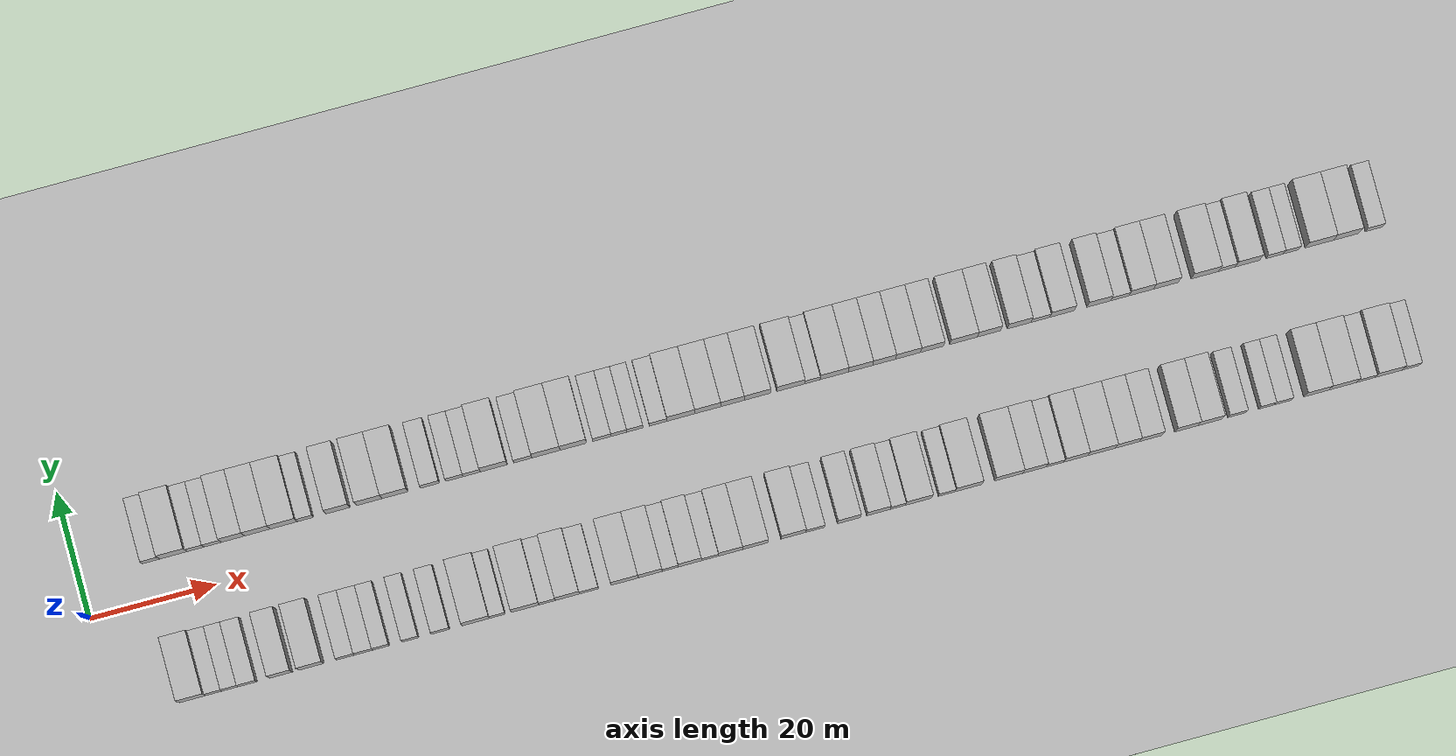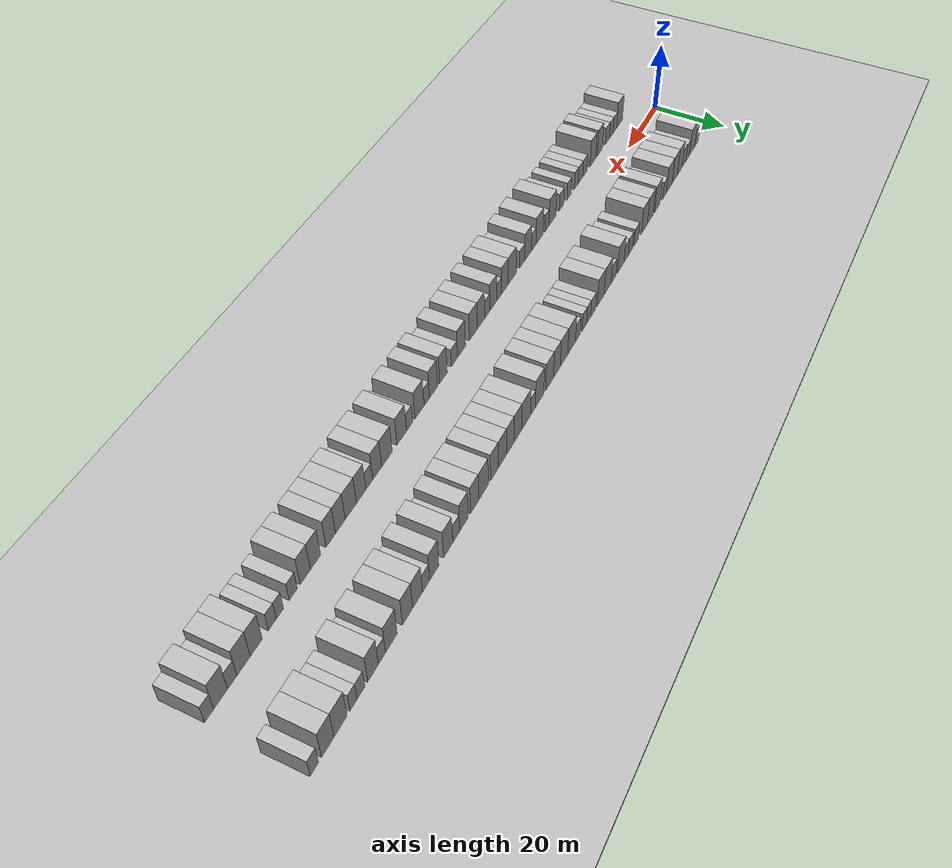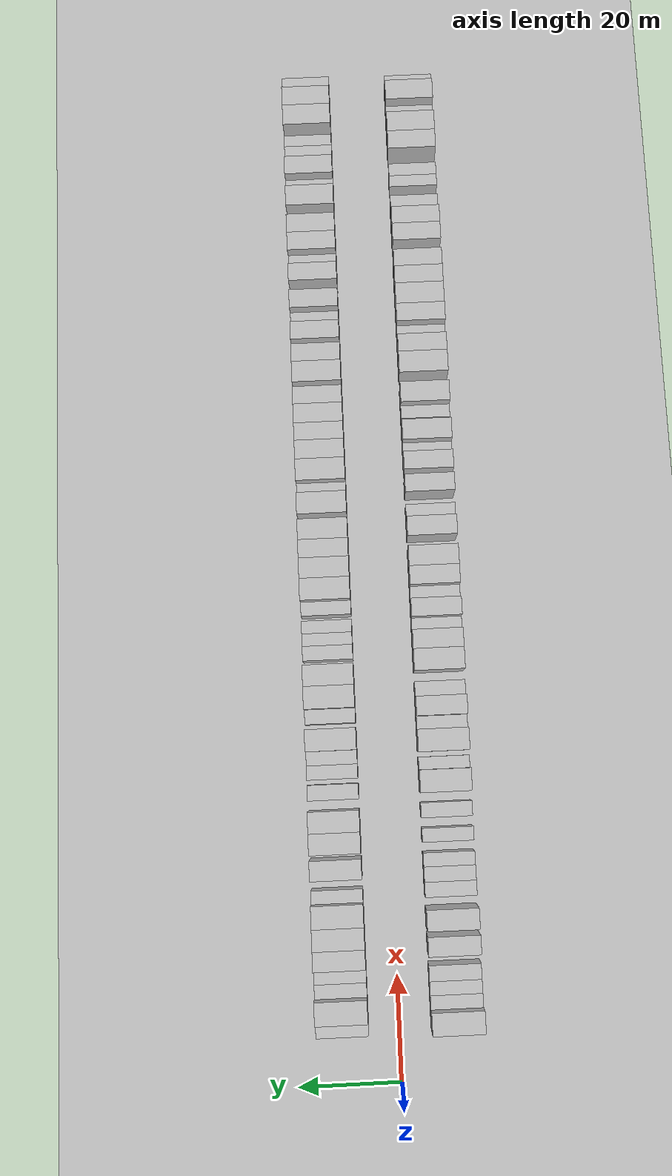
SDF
<?xml version="1.0" encoding="utf-8"?>

<sdf version="1.6">

   <world name="default">

      <gui fullscreen="0">

         <camera name="user_camera">

            <pose>-15 0 4.57585 0 0 0</pose>

            <view_controller>orbit</view_controller>

         </camera>

      </gui>

      <scene>

         <sky>

           <clouds>

             <speed>12</speed>

           </clouds>

         </sky>

         <ambient>0.4 0.4 0.4 1</ambient>

         <background>0.7 0.7 0.7 1</background>

         <shadows>1</shadows>

      </scene>

      <gravity>0 0 -9.8066</gravity>

      <magnetic_field>6e-06 2.3e-05 -4.2e-05</magnetic_field>

      <physics default="0" name="default_physics" type="ode">

         <ode>

            <solver>

               <type>quick</type>

               <iters>10</iters>

               <sor>1.0</sor>

               <use_dynamic_moi_rescaling>0</use_dynamic_moi_rescaling>

            </solver>

            <constraints>

               <cfm>0</cfm>

               <erp>0.2</erp>

               <contact_max_correcting_vel>100</contact_max_correcting_vel>

               <contact_surface_layer>0.001</contact_surface_layer>

            </constraints>

         </ode>

         <max_step_size>0.004</max_step_size>

         <real_time_factor>1</real_time_factor>

         <real_time_update_rate>250</real_time_update_rate>

      </physics>

      <light name="sun" type="directional">

         <cast_shadows>1</cast_shadows>

         <pose>0 0 10 0 0 0</pose>

         <diffuse>0.8 0.8 0.8 1</diffuse>

         <specular>0.2 0.2 0.2 1</specular>

         <attenuation>

            <range>1000</range>

            <constant>0.9</constant>

            <linear>0.01</linear>

            <quadratic>0.001</quadratic>

         </attenuation>

         <direction>-0.5 0.1 -0.9</direction>

      </light>

      <include>

         <name>ground_plane_1</name>

         <uri>model://HANNAS_ground_plane</uri>

         <pose>0 0 0  0 0 0</pose>

      </include>

      <include>

         <name>ground_plane_2</name>

         <uri>model://HANNAS_ground_plane</uri>

         <pose>100 0 0  0 0 0</pose>

      </include>

      <model name="building_1">

         <static>1</static>

         <pose frame="">11.3694 11.0000 0 0.000000 0.000000 1.570796</pose>

         <link name="link">

            <pose frame="">0 0 3.00 0 0 0</pose>

            <collision name="collision">

               <geometry>

                  <box>

                     <size>10.0000 2.7388 6.0000</size>

                  </box>

               </geometry>

               <max_contacts>10</max_contacts>

               <surface>

                  <contact>

                     <ode/>

                  </contact>

                  <bounce/>

                  <friction>

                     <torsional>

                        <ode/>

                     </torsional>

                     <ode/>

                  </friction>

               </surface>

            </collision>

            <visual name="visual">

               <cast_shadows>0</cast_shadows>

               <geometry>

                  <box>

                     <size>10.0000 2.7388 6.0000</size>

                  </box>

               </geometry>

               <material>

                  <script>

                     <uri>model://HANNAS_wall/materials/scripts</uri>

                     <uri>model://HANNAS_wall/materials/textures</uri>

                     <name>vrc/HANNAS_wall</name>

                  </script>

               </material>

            </visual>

            <self_collide>0</self_collide>

            <enable_wind>0</enable_wind>

            <kinematic>0</kinematic>

         </link>

      </model>

      <model name="building_2">

         <static>1</static>

         <pose frame="">14.9033 11.0000 0 0.000000 0.000000 1.570796</pose>

         <link name="link">

            <pose frame="">0 0 4.50 0 0 0</pose>

            <collision name="collision">

               <geometry>

                  <box>

                     <size>10.0000 4.3290 9.0000</size>

                  </box>

               </geometry>

               <max_contacts>10</max_contacts>

               <surface>

                  <contact>

                     <ode/>

                  </contact>

                  <bounce/>

                  <friction>

                     <torsional>

                        <ode/>

                     </torsional>

                     <ode/>

                  </friction>

               </surface>

            </collision>

            <visual name="visual">

               <cast_shadows>0</cast_shadows>

               <geometry>

                  <box>

                     <size>10.0000 4.3290 9.0000</size>

                  </box>

               </geometry>

               <material>

                  <script>

                     <uri>model://HANNAS_wall/materials/scripts</uri>

                     <uri>model://HANNAS_wall/materials/textures</uri>

                     <name>vrc/HANNAS_wall</name>

                  </script>

               </material>

            </visual>

            <self_collide>0</self_collide>

            <enable_wind>0</enable_wind>

            <kinematic>0</kinematic>

         </link>

      </model>

      <model name="building_3">

         <static>1</static>

         <pose frame="">18.3918 11.0000 0 0.000000 0.000000 1.570796</pose>

         <link name="link">

            <pose frame="">0 0 3.00 0 0 0</pose>

            <collision name="collision">

               <geometry>

                  <box>

                     <size>10.0000 2.6480 6.0000</size>

                  </box>

               </geometry>

               <max_contacts>10</max_contacts>

               <surface>

                  <contact>

                     <ode/>

                  </contact>

                  <bounce/>

                  <friction>

                     <torsional>

                        <ode/>

                     </torsional>

                     <ode/>

                  </friction>

               </surface>

            </collision>

            <visual name="visual">

               <cast_shadows>0</cast_shadows>

               <geometry>

                  <box>

                     <size>10.0000 2.6480 6.0000</size>

                  </box>

               </geometry>

               <material>

                  <script>

                     <uri>model://HANNAS_wall/materials/scripts</uri>

                     <uri>model://HANNAS_wall/materials/textures</uri>

                     <name>vrc/HANNAS_wall</name>

                  </script>

               </material>

            </visual>

            <self_collide>0</self_collide>

            <enable_wind>0</enable_wind>

            <kinematic>0</kinematic>

         </link>

      </model>

      <model name="building_4">

         <static>1</static>

         <pose frame="">21.0929 11.0000 0 0.000000 0.000000 1.570796</pose>

         <link name="link">

            <pose frame="">0 0 3.00 0 0 0</pose>

            <collision name="collision">

               <geometry>

                  <box>

                     <size>10.0000 2.7541 6.0000</size>

                  </box>

               </geometry>

               <max_contacts>10</max_contacts>

               <surface>

                  <contact>

                     <ode/>

                  </contact>

                  <bounce/>

                  <friction>

                     <torsional>

                        <ode/>

                     </torsional>

                     <ode/>

                  </friction>

               </surface>

            </collision>

            <visual name="visual">

               <cast_shadows>0</cast_shadows>

               <geometry>

                  <box>

                     <size>10.0000 2.7541 6.0000</size>

                  </box>

               </geometry>

               <material>

                  <script>

                     <uri>model://HANNAS_wall/materials/scripts</uri>

                     <uri>model://HANNAS_wall/materials/textures</uri>

                     <name>vrc/HANNAS_wall</name>

                  </script>

               </material>

            </visual>

            <self_collide>0</self_collide>

            <enable_wind>0</enable_wind>

            <kinematic>0</kinematic>

         </link>

      </model>

      <model name="building_5">

         <static>1</static>

         <pose frame="">24.3036 11.0000 0 0.000000 0.000000 1.570796</pose>

         <link name="link">

            <pose frame="">0 0 4.50 0 0 0</pose>

            <collision name="collision">

               <geometry>

                  <box>

                     <size>10.0000 3.6674 9.0000</size>

                  </box>

               </geometry>

               <max_contacts>10</max_contacts>

               <surface>

                  <contact>

                     <ode/>

                  </contact>

                  <bounce/>

                  <friction>

                     <torsional>

                        <ode/>

                     </torsional>

                     <ode/>

                  </friction>

               </surface>

            </collision>

            <visual name="visual">

               <cast_shadows>0</cast_shadows>

               <geometry>

                  <box>

                     <size>10.0000 3.6674 9.0000</size>

                  </box>

               </geometry>

               <material>

                  <script>

                     <uri>model://HANNAS_wall/materials/scripts</uri>

                     <uri>model://HANNAS_wall/materials/textures</uri>

                     <name>vrc/HANNAS_wall</name>

                  </script>

               </material>

            </visual>

            <self_collide>0</self_collide>

            <enable_wind>0</enable_wind>

            <kinematic>0</kinematic>

         </link>

      </model>

      <model name="building_6">

         <static>1</static>

         <pose frame="">28.1631 11.0000 0 0.000000 0.000000 1.570796</pose>

         <link name="link">

            <pose frame="">0 0 4.50 0 0 0</pose>

            <collision name="collision">

               <geometry>

                  <box>

                     <size>10.0000 4.0515 9.0000</size>

                  </box>

               </geometry>

               <max_contacts>10</max_contacts>

               <surface>

                  <contact>

                     <ode/>

                  </contact>

                  <bounce/>

                  <friction>

                     <torsional>

                        <ode/>

                     </torsional>

                     <ode/>

                  </friction>

               </surface>

            </collision>

            <visual name="visual">

               <cast_shadows>0</cast_shadows>

               <geometry>

                  <box>

                     <size>10.0000 4.0515 9.0000</size>

                  </box>

               </geometry>

               <material>

                  <script>

                     <uri>model://HANNAS_wall/materials/scripts</uri>

                     <uri>model://HANNAS_wall/materials/textures</uri>

                     <name>vrc/HANNAS_wall</name>

                  </script>

               </material>

            </visual>

            <self_collide>0</self_collide>

            <enable_wind>0</enable_wind>

            <kinematic>0</kinematic>

         </link>

      </model>

      <model name="building_7">

         <static>1</static>

         <pose frame="">32.3387 11.0000 0 0.000000 0.000000 1.570796</pose>

         <link name="link">

            <pose frame="">0 0 4.50 0 0 0</pose>

            <collision name="collision">

               <geometry>

                  <box>

                     <size>10.0000 4.2998 9.0000</size>

                  </box>

               </geometry>

               <max_contacts>10</max_contacts>

               <surface>

                  <contact>

                     <ode/>

                  </contact>

                  <bounce/>

                  <friction>

                     <torsional>

                        <ode/>

                     </torsional>

                     <ode/>

                  </friction>

               </surface>

            </collision>

            <visual name="visual">

               <cast_shadows>0</cast_shadows>

               <geometry>

                  <box>

                     <size>10.0000 4.2998 9.0000</size>

                  </box>

               </geometry>

               <material>

                  <script>

                     <uri>model://HANNAS_wall/materials/scripts</uri>

                     <uri>model://HANNAS_wall/materials/textures</uri>

                     <name>vrc/HANNAS_wall</name>

                  </script>

               </material>

            </visual>

            <self_collide>0</self_collide>

            <enable_wind>0</enable_wind>

            <kinematic>0</kinematic>

         </link>

      </model>

      <model name="building_8">

         <static>1</static>

         <pose frame="">35.7635 11.0000 0 0.000000 0.000000 1.570796</pose>

         <link name="link">

            <pose frame="">0 0 3.00 0 0 0</pose>

            <collision name="collision">

               <geometry>

                  <box>

                     <size>10.0000 2.5498 6.0000</size>

                  </box>

               </geometry>

               <max_contacts>10</max_contacts>

               <surface>

                  <contact>

                     <ode/>

                  </contact>

                  <bounce/>

                  <friction>

                     <torsional>

                        <ode/>

                     </torsional>

                     <ode/>

                  </friction>

               </surface>

            </collision>

            <visual name="visual">

               <cast_shadows>0</cast_shadows>

               <geometry>

                  <box>

                     <size>10.0000 2.5498 6.0000</size>

                  </box>

               </geometry>

               <material>

                  <script>

                     <uri>model://HANNAS_wall/materials/scripts</uri>

                     <uri>model://HANNAS_wall/materials/textures</uri>

                     <name>vrc/HANNAS_wall</name>

                  </script>

               </material>

            </visual>

            <self_collide>0</self_collide>

            <enable_wind>0</enable_wind>

            <kinematic>0</kinematic>

         </link>

      </model>

      <model name="building_9">

         <static>1</static>

         <pose frame="">40.9391 11.0000 0 0.000000 0.000000 1.570796</pose>

         <link name="link">

            <pose frame="">0 0 4.50 0 0 0</pose>

            <collision name="collision">

               <geometry>

                  <box>

                     <size>10.0000 3.8014 9.0000</size>

                  </box>

               </geometry>

               <max_contacts>10</max_contacts>

               <surface>

                  <contact>

                     <ode/>

                  </contact>

                  <bounce/>

                  <friction>

                     <torsional>

                        <ode/>

                     </torsional>

                     <ode/>

                  </friction>

               </surface>

            </collision>

            <visual name="visual">

               <cast_shadows>0</cast_shadows>

               <geometry>

                  <box>

                     <size>10.0000 3.8014 9.0000</size>

                  </box>

               </geometry>

               <material>

                  <script>

                     <uri>model://HANNAS_wall/materials/scripts</uri>

                     <uri>model://HANNAS_wall/materials/textures</uri>

                     <name>vrc/HANNAS_wall</name>

                  </script>

               </material>

            </visual>

            <self_collide>0</self_collide>

            <enable_wind>0</enable_wind>

            <kinematic>0</kinematic>

         </link>

      </model>

      <model name="building_10">

         <static>1</static>

         <pose frame="">45.8664 11.0000 0 0.000000 0.000000 1.570796</pose>

         <link name="link">

            <pose frame="">0 0 4.50 0 0 0</pose>

            <collision name="collision">

               <geometry>

                  <box>

                     <size>10.0000 4.0533 9.0000</size>

                  </box>

               </geometry>

               <max_contacts>10</max_contacts>

               <surface>

                  <contact>

                     <ode/>

                  </contact>

                  <bounce/>

                  <friction>

                     <torsional>

                        <ode/>

                     </torsional>

                     <ode/>

                  </friction>

               </surface>

            </collision>

            <visual name="visual">

               <cast_shadows>0</cast_shadows>

               <geometry>

                  <box>

                     <size>10.0000 4.0533 9.0000</size>

                  </box>

               </geometry>

               <material>

                  <script>

                     <uri>model://HANNAS_wall/materials/scripts</uri>

                     <uri>model://HANNAS_wall/materials/textures</uri>

                     <name>vrc/HANNAS_wall</name>

                  </script>

               </material>

            </visual>

            <self_collide>0</self_collide>

            <enable_wind>0</enable_wind>

            <kinematic>0</kinematic>

         </link>

      </model>

      <model name="building_11">

         <static>1</static>

         <pose frame="">49.9554 11.0000 0 0.000000 0.000000 1.570796</pose>

         <link name="link">

            <pose frame="">0 0 4.50 0 0 0</pose>

            <collision name="collision">

               <geometry>

                  <box>

                     <size>10.0000 4.1247 9.0000</size>

                  </box>

               </geometry>

               <max_contacts>10</max_contacts>

               <surface>

                  <contact>

                     <ode/>

                  </contact>

                  <bounce/>

                  <friction>

                     <torsional>

                        <ode/>

                     </torsional>

                     <ode/>

                  </friction>

               </surface>

            </collision>

            <visual name="visual">

               <cast_shadows>0</cast_shadows>

               <geometry>

                  <box>

                     <size>10.0000 4.1247 9.0000</size>

                  </box>

               </geometry>

               <material>

                  <script>

                     <uri>model://HANNAS_wall/materials/scripts</uri>

                     <uri>model://HANNAS_wall/materials/textures</uri>

                     <name>vrc/HANNAS_wall</name>

                  </script>

               </material>

            </visual>

            <self_collide>0</self_collide>

            <enable_wind>0</enable_wind>

            <kinematic>0</kinematic>

         </link>

      </model>

      <model name="building_12">

         <static>1</static>

         <pose frame="">55.5107 11.0000 0 0.000000 0.000000 1.570796</pose>

         <link name="link">

            <pose frame="">0 0 3.00 0 0 0</pose>

            <collision name="collision">

               <geometry>

                  <box>

                     <size>10.0000 2.9859 6.0000</size>

                  </box>

               </geometry>

               <max_contacts>10</max_contacts>

               <surface>

                  <contact>

                     <ode/>

                  </contact>

                  <bounce/>

                  <friction>

                     <torsional>

                        <ode/>

                     </torsional>

                     <ode/>

                  </friction>

               </surface>

            </collision>

            <visual name="visual">

               <cast_shadows>0</cast_shadows>

               <geometry>

                  <box>

                     <size>10.0000 2.9859 6.0000</size>

                  </box>

               </geometry>

               <material>

                  <script>

                     <uri>model://HANNAS_wall/materials/scripts</uri>

                     <uri>model://HANNAS_wall/materials/textures</uri>

                     <name>vrc/HANNAS_wall</name>

                  </script>

               </material>

            </visual>

            <self_collide>0</self_collide>

            <enable_wind>0</enable_wind>

            <kinematic>0</kinematic>

         </link>

      </model>

      <model name="building_13">

         <static>1</static>

         <pose frame="">59.3820 11.0000 0 0.000000 0.000000 1.570796</pose>

         <link name="link">

            <pose frame="">0 0 3.00 0 0 0</pose>

            <collision name="collision">

               <geometry>

                  <box>

                     <size>10.0000 2.7569 6.0000</size>

                  </box>

               </geometry>

               <max_contacts>10</max_contacts>

               <surface>

                  <contact>

                     <ode/>

                  </contact>

                  <bounce/>

                  <friction>

                     <torsional>

                        <ode/>

                     </torsional>

                     <ode/>

                  </friction>

               </surface>

            </collision>

            <visual name="visual">

               <cast_shadows>0</cast_shadows>

               <geometry>

                  <box>

                     <size>10.0000 2.7569 6.0000</size>

                  </box>

               </geometry>

               <material>

                  <script>

                     <uri>model://HANNAS_wall/materials/scripts</uri>

                     <uri>model://HANNAS_wall/materials/textures</uri>

                     <name>vrc/HANNAS_wall</name>

                  </script>

               </material>

            </visual>

            <self_collide>0</self_collide>

            <enable_wind>0</enable_wind>

            <kinematic>0</kinematic>

         </link>

      </model>

      <model name="building_14">

         <static>1</static>

         <pose frame="">62.1194 11.0000 0 0.000000 0.000000 1.570796</pose>

         <link name="link">

            <pose frame="">0 0 3.00 0 0 0</pose>

            <collision name="collision">

               <geometry>

                  <box>

                     <size>10.0000 2.7179 6.0000</size>

                  </box>

               </geometry>

               <max_contacts>10</max_contacts>

               <surface>

                  <contact>

                     <ode/>

                  </contact>

                  <bounce/>

                  <friction>

                     <torsional>

                        <ode/>

                     </torsional>

                     <ode/>

                  </friction>

               </surface>

            </collision>

            <visual name="visual">

               <cast_shadows>0</cast_shadows>

               <geometry>

                  <box>

                     <size>10.0000 2.7179 6.0000</size>

                  </box>

               </geometry>

               <material>

                  <script>

                     <uri>model://HANNAS_wall/materials/scripts</uri>

                     <uri>model://HANNAS_wall/materials/textures</uri>

                     <name>vrc/HANNAS_wall</name>

                  </script>

               </material>

            </visual>

            <self_collide>0</self_collide>

            <enable_wind>0</enable_wind>

            <kinematic>0</kinematic>

         </link>

      </model>

      <model name="building_15">

         <static>1</static>

         <pose frame="">65.6115 11.0000 0 0.000000 0.000000 1.570796</pose>

         <link name="link">

            <pose frame="">0 0 4.50 0 0 0</pose>

            <collision name="collision">

               <geometry>

                  <box>

                     <size>10.0000 4.2663 9.0000</size>

                  </box>

               </geometry>

               <max_contacts>10</max_contacts>

               <surface>

                  <contact>

                     <ode/>

                  </contact>

                  <bounce/>

                  <friction>

                     <torsional>

                        <ode/>

                     </torsional>

                     <ode/>

                  </friction>

               </surface>

            </collision>

            <visual name="visual">

               <cast_shadows>0</cast_shadows>

               <geometry>

                  <box>

                     <size>10.0000 4.2663 9.0000</size>

                  </box>

               </geometry>

               <material>

                  <script>

                     <uri>model://HANNAS_wall/materials/scripts</uri>

                     <uri>model://HANNAS_wall/materials/textures</uri>

                     <name>vrc/HANNAS_wall</name>

                  </script>

               </material>

            </visual>

            <self_collide>0</self_collide>

            <enable_wind>0</enable_wind>

            <kinematic>0</kinematic>

         </link>

      </model>

      <model name="building_16">

         <static>1</static>

         <pose frame="">70.1960 11.0000 0 0.000000 0.000000 1.570796</pose>

         <link name="link">

            <pose frame="">0 0 3.00 0 0 0</pose>

            <collision name="collision">

               <geometry>

                  <box>

                     <size>10.0000 2.9028 6.0000</size>

                  </box>

               </geometry>

               <max_contacts>10</max_contacts>

               <surface>

                  <contact>

                     <ode/>

                  </contact>

                  <bounce/>

                  <friction>

                     <torsional>

                        <ode/>

                     </torsional>

                     <ode/>

                  </friction>

               </surface>

            </collision>

            <visual name="visual">

               <cast_shadows>0</cast_shadows>

               <geometry>

                  <box>

                     <size>10.0000 2.9028 6.0000</size>

                  </box>

               </geometry>

               <material>

                  <script>

                     <uri>model://HANNAS_wall/materials/scripts</uri>

                     <uri>model://HANNAS_wall/materials/textures</uri>

                     <name>vrc/HANNAS_wall</name>

                  </script>

               </material>

            </visual>

            <self_collide>0</self_collide>

            <enable_wind>0</enable_wind>

            <kinematic>0</kinematic>

         </link>

      </model>

      <model name="building_17">

         <static>1</static>

         <pose frame="">73.8733 11.0000 0 0.000000 0.000000 1.570796</pose>

         <link name="link">

            <pose frame="">0 0 4.50 0 0 0</pose>

            <collision name="collision">

               <geometry>

                  <box>

                     <size>10.0000 4.4518 9.0000</size>

                  </box>

               </geometry>

               <max_contacts>10</max_contacts>

               <surface>

                  <contact>

                     <ode/>

                  </contact>

                  <bounce/>

                  <friction>

                     <torsional>

                        <ode/>

                     </torsional>

                     <ode/>

                  </friction>

               </surface>

            </collision>

            <visual name="visual">

               <cast_shadows>0</cast_shadows>

               <geometry>

                  <box>

                     <size>10.0000 4.4518 9.0000</size>

                  </box>

               </geometry>

               <material>

                  <script>

                     <uri>model://HANNAS_wall/materials/scripts</uri>

                     <uri>model://HANNAS_wall/materials/textures</uri>

                     <name>vrc/HANNAS_wall</name>

                  </script>

               </material>

            </visual>

            <self_collide>0</self_collide>

            <enable_wind>0</enable_wind>

            <kinematic>0</kinematic>

         </link>

      </model>

      <model name="building_18">

         <static>1</static>

         <pose frame="">78.1906 11.0000 0 0.000000 0.000000 1.570796</pose>

         <link name="link">

            <pose frame="">0 0 4.50 0 0 0</pose>

            <collision name="collision">

               <geometry>

                  <box>

                     <size>10.0000 4.1828 9.0000</size>

                  </box>

               </geometry>

               <max_contacts>10</max_contacts>

               <surface>

                  <contact>

                     <ode/>

                  </contact>

                  <bounce/>

                  <friction>

                     <torsional>

                        <ode/>

                     </torsional>

                     <ode/>

                  </friction>

               </surface>

            </collision>

            <visual name="visual">

               <cast_shadows>0</cast_shadows>

               <geometry>

                  <box>

                     <size>10.0000 4.1828 9.0000</size>

                  </box>

               </geometry>

               <material>

                  <script>

                     <uri>model://HANNAS_wall/materials/scripts</uri>

                     <uri>model://HANNAS_wall/materials/textures</uri>

                     <name>vrc/HANNAS_wall</name>

                  </script>

               </material>

            </visual>

            <self_collide>0</self_collide>

            <enable_wind>0</enable_wind>

            <kinematic>0</kinematic>

         </link>

      </model>

      <model name="building_19">

         <static>1</static>

         <pose frame="">82.7382 11.0000 0 0.000000 0.000000 1.570796</pose>

         <link name="link">

            <pose frame="">0 0 3.00 0 0 0</pose>

            <collision name="collision">

               <geometry>

                  <box>

                     <size>10.0000 2.9123 6.0000</size>

                  </box>

               </geometry>

               <max_contacts>10</max_contacts>

               <surface>

                  <contact>

                     <ode/>

                  </contact>

                  <bounce/>

                  <friction>

                     <torsional>

                        <ode/>

                     </torsional>

                     <ode/>

                  </friction>

               </surface>

            </collision>

            <visual name="visual">

               <cast_shadows>0</cast_shadows>

               <geometry>

                  <box>

                     <size>10.0000 2.9123 6.0000</size>

                  </box>

               </geometry>

               <material>

                  <script>

                     <uri>model://HANNAS_wall/materials/scripts</uri>

                     <uri>model://HANNAS_wall/materials/textures</uri>

                     <name>vrc/HANNAS_wall</name>

                  </script>

               </material>

            </visual>

            <self_collide>0</self_collide>

            <enable_wind>0</enable_wind>

            <kinematic>0</kinematic>

         </link>

      </model>

      <model name="building_20">

         <static>1</static>

         <pose frame="">85.4375 11.0000 0 0.000000 0.000000 1.570796</pose>

         <link name="link">

            <pose frame="">0 0 3.00 0 0 0</pose>

            <collision name="collision">

               <geometry>

                  <box>

                     <size>10.0000 2.4862 6.0000</size>

                  </box>

               </geometry>

               <max_contacts>10</max_contacts>

               <surface>

                  <contact>

                     <ode/>

                  </contact>

                  <bounce/>

                  <friction>

                     <torsional>

                        <ode/>

                     </torsional>

                     <ode/>

                  </friction>

               </surface>

            </collision>

            <visual name="visual">

               <cast_shadows>0</cast_shadows>

               <geometry>

                  <box>

                     <size>10.0000 2.4862 6.0000</size>

                  </box>

               </geometry>

               <material>

                  <script>

                     <uri>model://HANNAS_wall/materials/scripts</uri>

                     <uri>model://HANNAS_wall/materials/textures</uri>

                     <name>vrc/HANNAS_wall</name>

                  </script>

               </material>

            </visual>

            <self_collide>0</self_collide>

            <enable_wind>0</enable_wind>

            <kinematic>0</kinematic>

         </link>

      </model>

      <model name="building_21">

         <static>1</static>

         <pose frame="">87.9598 11.0000 0 0.000000 0.000000 1.570796</pose>

         <link name="link">

            <pose frame="">0 0 3.00 0 0 0</pose>

            <collision name="collision">

               <geometry>

                  <box>

                     <size>10.0000 2.5585 6.0000</size>

                  </box>

               </geometry>

               <max_contacts>10</max_contacts>

               <surface>

                  <contact>

                     <ode/>

                  </contact>

                  <bounce/>

                  <friction>

                     <torsional>

                        <ode/>

                     </torsional>

                     <ode/>

                  </friction>

               </surface>

            </collision>

            <visual name="visual">

               <cast_shadows>0</cast_shadows>

               <geometry>

                  <box>

                     <size>10.0000 2.5585 6.0000</size>

                  </box>

               </geometry>

               <material>

                  <script>

                     <uri>model://HANNAS_wall/materials/scripts</uri>

                     <uri>model://HANNAS_wall/materials/textures</uri>

                     <name>vrc/HANNAS_wall</name>

                  </script>

               </material>

            </visual>

            <self_collide>0</self_collide>

            <enable_wind>0</enable_wind>

            <kinematic>0</kinematic>

         </link>

      </model>

      <model name="building_22">

         <static>1</static>

         <pose frame="">91.6398 11.0000 0 0.000000 0.000000 1.570796</pose>

         <link name="link">

            <pose frame="">0 0 3.00 0 0 0</pose>

            <collision name="collision">

               <geometry>

                  <box>

                     <size>10.0000 2.8016 6.0000</size>

                  </box>

               </geometry>

               <max_contacts>10</max_contacts>

               <surface>

                  <contact>

                     <ode/>

                  </contact>

                  <bounce/>

                  <friction>

                     <torsional>

                        <ode/>

                     </torsional>

                     <ode/>

                  </friction>

               </surface>

            </collision>

            <visual name="visual">

               <cast_shadows>0</cast_shadows>

               <geometry>

                  <box>

                     <size>10.0000 2.8016 6.0000</size>

                  </box>

               </geometry>

               <material>

                  <script>

                     <uri>model://HANNAS_wall/materials/scripts</uri>

                     <uri>model://HANNAS_wall/materials/textures</uri>

                     <name>vrc/HANNAS_wall</name>

                  </script>

               </material>

            </visual>

            <self_collide>0</self_collide>

            <enable_wind>0</enable_wind>

            <kinematic>0</kinematic>

         </link>

      </model>

      <model name="building_23">

         <static>1</static>

         <pose frame="">95.2498 11.0000 0 0.000000 0.000000 1.570796</pose>

         <link name="link">

            <pose frame="">0 0 4.50 0 0 0</pose>

            <collision name="collision">

               <geometry>

                  <box>

                     <size>10.0000 4.4185 9.0000</size>

                  </box>

               </geometry>

               <max_contacts>10</max_contacts>

               <surface>

                  <contact>

                     <ode/>

                  </contact>

                  <bounce/>

                  <friction>

                     <torsional>

                        <ode/>

                     </torsional>

                     <ode/>

                  </friction>

               </surface>

            </collision>

            <visual name="visual">

               <cast_shadows>0</cast_shadows>

               <geometry>

                  <box>

                     <size>10.0000 4.4185 9.0000</size>

                  </box>

               </geometry>

               <material>

                  <script>

                     <uri>model://HANNAS_wall/materials/scripts</uri>

                     <uri>model://HANNAS_wall/materials/textures</uri>

                     <name>vrc/HANNAS_wall</name>

                  </script>

               </material>

            </visual>

            <self_collide>0</self_collide>

            <enable_wind>0</enable_wind>

            <kinematic>0</kinematic>

         </link>

      </model>

      <model name="building_24">

         <static>1</static>

         <pose frame="">99.5107 11.0000 0 0.000000 0.000000 1.570796</pose>

         <link name="link">

            <pose frame="">0 0 4.50 0 0 0</pose>

            <collision name="collision">

               <geometry>

                  <box>

                     <size>10.0000 4.1032 9.0000</size>

                  </box>

               </geometry>

               <max_contacts>10</max_contacts>

               <surface>

                  <contact>

                     <ode/>

                  </contact>

                  <bounce/>

                  <friction>

                     <torsional>

                        <ode/>

                     </torsional>

                     <ode/>

                  </friction>

               </surface>

            </collision>

            <visual name="visual">

               <cast_shadows>0</cast_shadows>

               <geometry>

                  <box>

                     <size>10.0000 4.1032 9.0000</size>

                  </box>

               </geometry>

               <material>

                  <script>

                     <uri>model://HANNAS_wall/materials/scripts</uri>

                     <uri>model://HANNAS_wall/materials/textures</uri>

                     <name>vrc/HANNAS_wall</name>

                  </script>

               </material>

            </visual>

            <self_collide>0</self_collide>

            <enable_wind>0</enable_wind>

            <kinematic>0</kinematic>

         </link>

      </model>

      <model name="building_25">

         <static>1</static>

         <pose frame="">103.4110 11.0000 0 0.000000 0.000000 1.570796</pose>

         <link name="link">

            <pose frame="">0 0 4.50 0 0 0</pose>

            <collision name="collision">

               <geometry>

                  <box>

                     <size>10.0000 3.6974 9.0000</size>

                  </box>

               </geometry>

               <max_contacts>10</max_contacts>

               <surface>

                  <contact>

                     <ode/>

                  </contact>

                  <bounce/>

                  <friction>

                     <torsional>

                        <ode/>

                     </torsional>

                     <ode/>

                  </friction>

               </surface>

            </collision>

            <visual name="visual">

               <cast_shadows>0</cast_shadows>

               <geometry>

                  <box>

                     <size>10.0000 3.6974 9.0000</size>

                  </box>

               </geometry>

               <material>

                  <script>

                     <uri>model://HANNAS_wall/materials/scripts</uri>

                     <uri>model://HANNAS_wall/materials/textures</uri>

                     <name>vrc/HANNAS_wall</name>

                  </script>

               </material>

            </visual>

            <self_collide>0</self_collide>

            <enable_wind>0</enable_wind>

            <kinematic>0</kinematic>

         </link>

      </model>

      <model name="building_26">

         <static>1</static>

         <pose frame="">107.3547 11.0000 0 0.000000 0.000000 1.570796</pose>

         <link name="link">

            <pose frame="">0 0 4.50 0 0 0</pose>

            <collision name="collision">

               <geometry>

                  <box>

                     <size>10.0000 4.1900 9.0000</size>

                  </box>

               </geometry>

               <max_contacts>10</max_contacts>

               <surface>

                  <contact>

                     <ode/>

                  </contact>

                  <bounce/>

                  <friction>

                     <torsional>

                        <ode/>

                     </torsional>

                     <ode/>

                  </friction>

               </surface>

            </collision>

            <visual name="visual">

               <cast_shadows>0</cast_shadows>

               <geometry>

                  <box>

                     <size>10.0000 4.1900 9.0000</size>

                  </box>

               </geometry>

               <material>

                  <script>

                     <uri>model://HANNAS_wall/materials/scripts</uri>

                     <uri>model://HANNAS_wall/materials/textures</uri>

                     <name>vrc/HANNAS_wall</name>

                  </script>

               </material>

            </visual>

            <self_collide>0</self_collide>

            <enable_wind>0</enable_wind>

            <kinematic>0</kinematic>

         </link>

      </model>

      <model name="building_27">

         <static>1</static>

         <pose frame="">112.6648 11.0000 0 0.000000 0.000000 1.570796</pose>

         <link name="link">

            <pose frame="">0 0 4.50 0 0 0</pose>

            <collision name="collision">

               <geometry>

                  <box>

                     <size>10.0000 4.4302 9.0000</size>

                  </box>

               </geometry>

               <max_contacts>10</max_contacts>

               <surface>

                  <contact>

                     <ode/>

                  </contact>

                  <bounce/>

                  <friction>

                     <torsional>

                        <ode/>

                     </torsional>

                     <ode/>

                  </friction>

               </surface>

            </collision>

            <visual name="visual">

               <cast_shadows>0</cast_shadows>

               <geometry>

                  <box>

                     <size>10.0000 4.4302 9.0000</size>

                  </box>

               </geometry>

               <material>

                  <script>

                     <uri>model://HANNAS_wall/materials/scripts</uri>

                     <uri>model://HANNAS_wall/materials/textures</uri>

                     <name>vrc/HANNAS_wall</name>

                  </script>

               </material>

            </visual>

            <self_collide>0</self_collide>

            <enable_wind>0</enable_wind>

            <kinematic>0</kinematic>

         </link>

      </model>

      <model name="building_28">

         <static>1</static>

         <pose frame="">116.1045 11.0000 0 0.000000 0.000000 1.570796</pose>

         <link name="link">

            <pose frame="">0 0 3.00 0 0 0</pose>

            <collision name="collision">

               <geometry>

                  <box>

                     <size>10.0000 2.4492 6.0000</size>

                  </box>

               </geometry>

               <max_contacts>10</max_contacts>

               <surface>

                  <contact>

                     <ode/>

                  </contact>

                  <bounce/>

                  <friction>

                     <torsional>

                        <ode/>

                     </torsional>

                     <ode/>

                  </friction>

               </surface>

            </collision>

            <visual name="visual">

               <cast_shadows>0</cast_shadows>

               <geometry>

                  <box>

                     <size>10.0000 2.4492 6.0000</size>

                  </box>

               </geometry>

               <material>

                  <script>

                     <uri>model://HANNAS_wall/materials/scripts</uri>

                     <uri>model://HANNAS_wall/materials/textures</uri>

                     <name>vrc/HANNAS_wall</name>

                  </script>

               </material>

            </visual>

            <self_collide>0</self_collide>

            <enable_wind>0</enable_wind>

            <kinematic>0</kinematic>

         </link>

      </model>

      <model name="building_29">

         <static>1</static>

         <pose frame="">119.5563 11.0000 0 0.000000 0.000000 1.570796</pose>

         <link name="link">

            <pose frame="">0 0 4.50 0 0 0</pose>

            <collision name="collision">

               <geometry>

                  <box>

                     <size>10.0000 4.4545 9.0000</size>

                  </box>

               </geometry>

               <max_contacts>10</max_contacts>

               <surface>

                  <contact>

                     <ode/>

                  </contact>

                  <bounce/>

                  <friction>

                     <torsional>

                        <ode/>

                     </torsional>

                     <ode/>

                  </friction>

               </surface>

            </collision>

            <visual name="visual">

               <cast_shadows>0</cast_shadows>

               <geometry>

                  <box>

                     <size>10.0000 4.4545 9.0000</size>

                  </box>

               </geometry>

               <material>

                  <script>

                     <uri>model://HANNAS_wall/materials/scripts</uri>

                     <uri>model://HANNAS_wall/materials/textures</uri>

                     <name>vrc/HANNAS_wall</name>

                  </script>

               </material>

            </visual>

            <self_collide>0</self_collide>

            <enable_wind>0</enable_wind>

            <kinematic>0</kinematic>

         </link>

      </model>

      <model name="building_30">

         <static>1</static>

         <pose frame="">123.7197 11.0000 0 0.000000 0.000000 1.570796</pose>

         <link name="link">

            <pose frame="">0 0 4.50 0 0 0</pose>

            <collision name="collision">

               <geometry>

                  <box>

                     <size>10.0000 3.8723 9.0000</size>

                  </box>

               </geometry>

               <max_contacts>10</max_contacts>

               <surface>

                  <contact>

                     <ode/>

                  </contact>

                  <bounce/>

                  <friction>

                     <torsional>

                        <ode/>

                     </torsional>

                     <ode/>

                  </friction>

               </surface>

            </collision>

            <visual name="visual">

               <cast_shadows>0</cast_shadows>

               <geometry>

                  <box>

                     <size>10.0000 3.8723 9.0000</size>

                  </box>

               </geometry>

               <material>

                  <script>

                     <uri>model://HANNAS_wall/materials/scripts</uri>

                     <uri>model://HANNAS_wall/materials/textures</uri>

                     <name>vrc/HANNAS_wall</name>

                  </script>

               </material>

            </visual>

            <self_collide>0</self_collide>

            <enable_wind>0</enable_wind>

            <kinematic>0</kinematic>

         </link>

      </model>

      <model name="building_31">

         <static>1</static>

         <pose frame="">127.4697 11.0000 0 0.000000 0.000000 1.570796</pose>

         <link name="link">

            <pose frame="">0 0 4.50 0 0 0</pose>

            <collision name="collision">

               <geometry>

                  <box>

                     <size>10.0000 3.6276 9.0000</size>

                  </box>

               </geometry>

               <max_contacts>10</max_contacts>

               <surface>

                  <contact>

                     <ode/>

                  </contact>

                  <bounce/>

                  <friction>

                     <torsional>

                        <ode/>

                     </torsional>

                     <ode/>

                  </friction>

               </surface>

            </collision>

            <visual name="visual">

               <cast_shadows>0</cast_shadows>

               <geometry>

                  <box>

                     <size>10.0000 3.6276 9.0000</size>

                  </box>

               </geometry>

               <material>

                  <script>

                     <uri>model://HANNAS_wall/materials/scripts</uri>

                     <uri>model://HANNAS_wall/materials/textures</uri>

                     <name>vrc/HANNAS_wall</name>

                  </script>

               </material>

            </visual>

            <self_collide>0</self_collide>

            <enable_wind>0</enable_wind>

            <kinematic>0</kinematic>

         </link>

      </model>

      <model name="building_32">

         <static>1</static>

         <pose frame="">131.2735 11.0000 0 0.000000 0.000000 1.570796</pose>

         <link name="link">

            <pose frame="">0 0 4.50 0 0 0</pose>

            <collision name="collision">

               <geometry>

                  <box>

                     <size>10.0000 3.9799 9.0000</size>

                  </box>

               </geometry>

               <max_contacts>10</max_contacts>

               <surface>

                  <contact>

                     <ode/>

                  </contact>

                  <bounce/>

                  <friction>

                     <torsional>

                        <ode/>

                     </torsional>

                     <ode/>

                  </friction>

               </surface>

            </collision>

            <visual name="visual">

               <cast_shadows>0</cast_shadows>

               <geometry>

                  <box>

                     <size>10.0000 3.9799 9.0000</size>

                  </box>

               </geometry>

               <material>

                  <script>

                     <uri>model://HANNAS_wall/materials/scripts</uri>

                     <uri>model://HANNAS_wall/materials/textures</uri>

                     <name>vrc/HANNAS_wall</name>

                  </script>

               </material>

            </visual>

            <self_collide>0</self_collide>

            <enable_wind>0</enable_wind>

            <kinematic>0</kinematic>

         </link>

      </model>

      <model name="building_33">

         <static>1</static>

         <pose frame="">135.0868 11.0000 0 0.000000 0.000000 1.570796</pose>

         <link name="link">

            <pose frame="">0 0 4.50 0 0 0</pose>

            <collision name="collision">

               <geometry>

                  <box>

                     <size>10.0000 3.6468 9.0000</size>

                  </box>

               </geometry>

               <max_contacts>10</max_contacts>

               <surface>

                  <contact>

                     <ode/>

                  </contact>

                  <bounce/>

                  <friction>

                     <torsional>

                        <ode/>

                     </torsional>

                     <ode/>

                  </friction>

               </surface>

            </collision>

            <visual name="visual">

               <cast_shadows>0</cast_shadows>

               <geometry>

                  <box>

                     <size>10.0000 3.6468 9.0000</size>

                  </box>

               </geometry>

               <material>

                  <script>

                     <uri>model://HANNAS_wall/materials/scripts</uri>

                     <uri>model://HANNAS_wall/materials/textures</uri>

                     <name>vrc/HANNAS_wall</name>

                  </script>

               </material>

            </visual>

            <self_collide>0</self_collide>

            <enable_wind>0</enable_wind>

            <kinematic>0</kinematic>

         </link>

      </model>

      <model name="building_34">

         <static>1</static>

         <pose frame="">140.0975 11.0000 0 0.000000 0.000000 1.570796</pose>

         <link name="link">

            <pose frame="">0 0 4.50 0 0 0</pose>

            <collision name="collision">

               <geometry>

                  <box>

                     <size>10.0000 4.3745 9.0000</size>

                  </box>

               </geometry>

               <max_contacts>10</max_contacts>

               <surface>

                  <contact>

                     <ode/>

                  </contact>

                  <bounce/>

                  <friction>

                     <torsional>

                        <ode/>

                     </torsional>

                     <ode/>

                  </friction>

               </surface>

            </collision>

            <visual name="visual">

               <cast_shadows>0</cast_shadows>

               <geometry>

                  <box>

                     <size>10.0000 4.3745 9.0000</size>

                  </box>

               </geometry>

               <material>

                  <script>

                     <uri>model://HANNAS_wall/materials/scripts</uri>

                     <uri>model://HANNAS_wall/materials/textures</uri>

                     <name>vrc/HANNAS_wall</name>

                  </script>

               </material>

            </visual>

            <self_collide>0</self_collide>

            <enable_wind>0</enable_wind>

            <kinematic>0</kinematic>

         </link>

      </model>

      <model name="building_35">

         <static>1</static>

         <pose frame="">144.1498 11.0000 0 0.000000 0.000000 1.570796</pose>

         <link name="link">

            <pose frame="">0 0 4.50 0 0 0</pose>

            <collision name="collision">

               <geometry>

                  <box>

                     <size>10.0000 3.7302 9.0000</size>

                  </box>

               </geometry>

               <max_contacts>10</max_contacts>

               <surface>

                  <contact>

                     <ode/>

                  </contact>

                  <bounce/>

                  <friction>

                     <torsional>

                        <ode/>

                     </torsional>

                     <ode/>

                  </friction>

               </surface>

            </collision>

            <visual name="visual">

               <cast_shadows>0</cast_shadows>

               <geometry>

                  <box>

                     <size>10.0000 3.7302 9.0000</size>

                  </box>

               </geometry>

               <material>

                  <script>

                     <uri>model://HANNAS_wall/materials/scripts</uri>

                     <uri>model://HANNAS_wall/materials/textures</uri>

                     <name>vrc/HANNAS_wall</name>

                  </script>

               </material>

            </visual>

            <self_collide>0</self_collide>

            <enable_wind>0</enable_wind>

            <kinematic>0</kinematic>

         </link>

      </model>

      <model name="building_36">

         <static>1</static>

         <pose frame="">148.9083 11.0000 0 0.000000 0.000000 1.570796</pose>

         <link name="link">

            <pose frame="">0 0 4.50 0 0 0</pose>

            <collision name="collision">

               <geometry>

                  <box>

                     <size>10.0000 3.7869 9.0000</size>

                  </box>

               </geometry>

               <max_contacts>10</max_contacts>

               <surface>

                  <contact>

                     <ode/>

                  </contact>

                  <bounce/>

                  <friction>

                     <torsional>

                        <ode/>

                     </torsional>

                     <ode/>

                  </friction>

               </surface>

            </collision>

            <visual name="visual">

               <cast_shadows>0</cast_shadows>

               <geometry>

                  <box>

                     <size>10.0000 3.7869 9.0000</size>

                  </box>

               </geometry>

               <material>

                  <script>

                     <uri>model://HANNAS_wall/materials/scripts</uri>

                     <uri>model://HANNAS_wall/materials/textures</uri>

                     <name>vrc/HANNAS_wall</name>

                  </script>

               </material>

            </visual>

            <self_collide>0</self_collide>

            <enable_wind>0</enable_wind>

            <kinematic>0</kinematic>

         </link>

      </model>

      <model name="building_37">

         <static>1</static>

         <pose frame="">152.3015 11.0000 0 0.000000 0.000000 1.570796</pose>

         <link name="link">

            <pose frame="">0 0 3.00 0 0 0</pose>

            <collision name="collision">

               <geometry>

                  <box>

                     <size>10.0000 2.9994 6.0000</size>

                  </box>

               </geometry>

               <max_contacts>10</max_contacts>

               <surface>

                  <contact>

                     <ode/>

                  </contact>

                  <bounce/>

                  <friction>

                     <torsional>

                        <ode/>

                     </torsional>

                     <ode/>

                  </friction>

               </surface>

            </collision>

            <visual name="visual">

               <cast_shadows>0</cast_shadows>

               <geometry>

                  <box>

                     <size>10.0000 2.9994 6.0000</size>

                  </box>

               </geometry>

               <material>

                  <script>

                     <uri>model://HANNAS_wall/materials/scripts</uri>

                     <uri>model://HANNAS_wall/materials/textures</uri>

                     <name>vrc/HANNAS_wall</name>

                  </script>

               </material>

            </visual>

            <self_collide>0</self_collide>

            <enable_wind>0</enable_wind>

            <kinematic>0</kinematic>

         </link>

      </model>

      <model name="building_38">

         <static>1</static>

         <pose frame="">155.7456 11.0000 0 0.000000 0.000000 1.570796</pose>

         <link name="link">

            <pose frame="">0 0 4.50 0 0 0</pose>

            <collision name="collision">

               <geometry>

                  <box>

                     <size>10.0000 3.8888 9.0000</size>

                  </box>

               </geometry>

               <max_contacts>10</max_contacts>

               <surface>

                  <contact>

                     <ode/>

                  </contact>

                  <bounce/>

                  <friction>

                     <torsional>

                        <ode/>

                     </torsional>

                     <ode/>

                  </friction>

               </surface>

            </collision>

            <visual name="visual">

               <cast_shadows>0</cast_shadows>

               <geometry>

                  <box>

                     <size>10.0000 3.8888 9.0000</size>

                  </box>

               </geometry>

               <material>

                  <script>

                     <uri>model://HANNAS_wall/materials/scripts</uri>

                     <uri>model://HANNAS_wall/materials/textures</uri>

                     <name>vrc/HANNAS_wall</name>

                  </script>

               </material>

            </visual>

            <self_collide>0</self_collide>

            <enable_wind>0</enable_wind>

            <kinematic>0</kinematic>

         </link>

      </model>

      <model name="building_39">

         <static>1</static>

         <pose frame="">161.5662 11.0000 0 0.000000 0.000000 1.570796</pose>

         <link name="link">

            <pose frame="">0 0 4.50 0 0 0</pose>

            <collision name="collision">

               <geometry>

                  <box>

                     <size>10.0000 3.7523 9.0000</size>

                  </box>

               </geometry>

               <max_contacts>10</max_contacts>

               <surface>

                  <contact>

                     <ode/>

                  </contact>

                  <bounce/>

                  <friction>

                     <torsional>

                        <ode/>

                     </torsional>

                     <ode/>

                  </friction>

               </surface>

            </collision>

            <visual name="visual">

               <cast_shadows>0</cast_shadows>

               <geometry>

                  <box>

                     <size>10.0000 3.7523 9.0000</size>

                  </box>

               </geometry>

               <material>

                  <script>

                     <uri>model://HANNAS_wall/materials/scripts</uri>

                     <uri>model://HANNAS_wall/materials/textures</uri>

                     <name>vrc/HANNAS_wall</name>

                  </script>

               </material>

            </visual>

            <self_collide>0</self_collide>

            <enable_wind>0</enable_wind>

            <kinematic>0</kinematic>

         </link>

      </model>

      <model name="building_40">

         <static>1</static>

         <pose frame="">164.9139 11.0000 0 0.000000 0.000000 1.570796</pose>

         <link name="link">

            <pose frame="">0 0 3.00 0 0 0</pose>

            <collision name="collision">

               <geometry>

                  <box>

                     <size>10.0000 2.9432 6.0000</size>

                  </box>

               </geometry>

               <max_contacts>10</max_contacts>

               <surface>

                  <contact>

                     <ode/>

                  </contact>

                  <bounce/>

                  <friction>

                     <torsional>

                        <ode/>

                     </torsional>

                     <ode/>

                  </friction>

               </surface>

            </collision>

            <visual name="visual">

               <cast_shadows>0</cast_shadows>

               <geometry>

                  <box>

                     <size>10.0000 2.9432 6.0000</size>

                  </box>

               </geometry>

               <material>

                  <script>

                     <uri>model://HANNAS_wall/materials/scripts</uri>

                     <uri>model://HANNAS_wall/materials/textures</uri>

                     <name>vrc/HANNAS_wall</name>

                  </script>

               </material>

            </visual>

            <self_collide>0</self_collide>

            <enable_wind>0</enable_wind>

            <kinematic>0</kinematic>

         </link>

      </model>

      <model name="building_41">

         <static>1</static>

         <pose frame="">168.3362 11.0000 0 0.000000 0.000000 1.570796</pose>

         <link name="link">

            <pose frame="">0 0 4.50 0 0 0</pose>

            <collision name="collision">

               <geometry>

                  <box>

                     <size>10.0000 3.9013 9.0000</size>

                  </box>

               </geometry>

               <max_contacts>10</max_contacts>

               <surface>

                  <contact>

                     <ode/>

                  </contact>

                  <bounce/>

                  <friction>

                     <torsional>

                        <ode/>

                     </torsional>

                     <ode/>

                  </friction>

               </surface>

            </collision>

            <visual name="visual">

               <cast_shadows>0</cast_shadows>

               <geometry>

                  <box>

                     <size>10.0000 3.9013 9.0000</size>

                  </box>

               </geometry>

               <material>

                  <script>

                     <uri>model://HANNAS_wall/materials/scripts</uri>

                     <uri>model://HANNAS_wall/materials/textures</uri>

                     <name>vrc/HANNAS_wall</name>

                  </script>

               </material>

            </visual>

            <self_collide>0</self_collide>

            <enable_wind>0</enable_wind>

            <kinematic>0</kinematic>

         </link>

      </model>

      <model name="building_42">

         <static>1</static>

         <pose frame="">172.2730 11.0000 0 0.000000 0.000000 1.570796</pose>

         <link name="link">

            <pose frame="">0 0 4.50 0 0 0</pose>

            <collision name="collision">

               <geometry>

                  <box>

                     <size>10.0000 3.9724 9.0000</size>

                  </box>

               </geometry>

               <max_contacts>10</max_contacts>

               <surface>

                  <contact>

                     <ode/>

                  </contact>

                  <bounce/>

                  <friction>

                     <torsional>

                        <ode/>

                     </torsional>

                     <ode/>

                  </friction>

               </surface>

            </collision>

            <visual name="visual">

               <cast_shadows>0</cast_shadows>

               <geometry>

                  <box>

                     <size>10.0000 3.9724 9.0000</size>

                  </box>

               </geometry>

               <material>

                  <script>

                     <uri>model://HANNAS_wall/materials/scripts</uri>

                     <uri>model://HANNAS_wall/materials/textures</uri>

                     <name>vrc/HANNAS_wall</name>

                  </script>

               </material>

            </visual>

            <self_collide>0</self_collide>

            <enable_wind>0</enable_wind>

            <kinematic>0</kinematic>

         </link>

      </model>

      <model name="building_43">

         <static>1</static>

         <pose frame="">178.4589 11.0000 0 0.000000 0.000000 1.570796</pose>

         <link name="link">

            <pose frame="">0 0 4.50 0 0 0</pose>

            <collision name="collision">

               <geometry>

                  <box>

                     <size>10.0000 4.3993 9.0000</size>

                  </box>

               </geometry>

               <max_contacts>10</max_contacts>

               <surface>

                  <contact>

                     <ode/>

                  </contact>

                  <bounce/>

                  <friction>

                     <torsional>

                        <ode/>

                     </torsional>

                     <ode/>

                  </friction>

               </surface>

            </collision>

            <visual name="visual">

               <cast_shadows>0</cast_shadows>

               <geometry>

                  <box>

                     <size>10.0000 4.3993 9.0000</size>

                  </box>

               </geometry>

               <material>

                  <script>

                     <uri>model://HANNAS_wall/materials/scripts</uri>

                     <uri>model://HANNAS_wall/materials/textures</uri>

                     <name>vrc/HANNAS_wall</name>

                  </script>

               </material>

            </visual>

            <self_collide>0</self_collide>

            <enable_wind>0</enable_wind>

            <kinematic>0</kinematic>

         </link>

      </model>

      <model name="building_44">

         <static>1</static>

         <pose frame="">181.9692 11.0000 0 0.000000 0.000000 1.570796</pose>

         <link name="link">

            <pose frame="">0 0 3.00 0 0 0</pose>

            <collision name="collision">

               <geometry>

                  <box>

                     <size>10.0000 2.6214 6.0000</size>

                  </box>

               </geometry>

               <max_contacts>10</max_contacts>

               <surface>

                  <contact>

                     <ode/>

                  </contact>

                  <bounce/>

                  <friction>

                     <torsional>

                        <ode/>

                     </torsional>

                     <ode/>

                  </friction>

               </surface>

            </collision>

            <visual name="visual">

               <cast_shadows>0</cast_shadows>

               <geometry>

                  <box>

                     <size>10.0000 2.6214 6.0000</size>

                  </box>

               </geometry>

               <material>

                  <script>

                     <uri>model://HANNAS_wall/materials/scripts</uri>

                     <uri>model://HANNAS_wall/materials/textures</uri>

                     <name>vrc/HANNAS_wall</name>

                  </script>

               </material>

            </visual>

            <self_collide>0</self_collide>

            <enable_wind>0</enable_wind>

            <kinematic>0</kinematic>

         </link>

      </model>

      <model name="building_45">

         <static>1</static>

         <pose frame="">185.2407 11.0000 0 0.000000 0.000000 1.570796</pose>

         <link name="link">

            <pose frame="">0 0 4.50 0 0 0</pose>

            <collision name="collision">

               <geometry>

                  <box>

                     <size>10.0000 3.9215 9.0000</size>

                  </box>

               </geometry>

               <max_contacts>10</max_contacts>

               <surface>

                  <contact>

                     <ode/>

                  </contact>

                  <bounce/>

                  <friction>

                     <torsional>

                        <ode/>

                     </torsional>

                     <ode/>

                  </friction>

               </surface>

            </collision>

            <visual name="visual">

               <cast_shadows>0</cast_shadows>

               <geometry>

                  <box>

                     <size>10.0000 3.9215 9.0000</size>

                  </box>

               </geometry>

               <material>

                  <script>

                     <uri>model://HANNAS_wall/materials/scripts</uri>

                     <uri>model://HANNAS_wall/materials/textures</uri>

                     <name>vrc/HANNAS_wall</name>

                  </script>

               </material>

            </visual>

            <self_collide>0</self_collide>

            <enable_wind>0</enable_wind>

            <kinematic>0</kinematic>

         </link>

      </model>

      <model name="building_46">

         <static>1</static>

         <pose frame="">189.5925 11.0000 0 0.000000 0.000000 1.570796</pose>

         <link name="link">

            <pose frame="">0 0 3.00 0 0 0</pose>

            <collision name="collision">

               <geometry>

                  <box>

                     <size>10.0000 2.7821 6.0000</size>

                  </box>

               </geometry>

               <max_contacts>10</max_contacts>

               <surface>

                  <contact>

                     <ode/>

                  </contact>

                  <bounce/>

                  <friction>

                     <torsional>

                        <ode/>

                     </torsional>

                     <ode/>

                  </friction>

               </surface>

            </collision>

            <visual name="visual">

               <cast_shadows>0</cast_shadows>

               <geometry>

                  <box>

                     <size>10.0000 2.7821 6.0000</size>

                  </box>

               </geometry>

               <material>

                  <script>

                     <uri>model://HANNAS_wall/materials/scripts</uri>

                     <uri>model://HANNAS_wall/materials/textures</uri>

                     <name>vrc/HANNAS_wall</name>

                  </script>

               </material>

            </visual>

            <self_collide>0</self_collide>

            <enable_wind>0</enable_wind>

            <kinematic>0</kinematic>

         </link>

      </model>

      <model name="building_47">

         <static>1</static>

         <pose frame="">192.2112 11.0000 0 0.000000 0.000000 1.570796</pose>

         <link name="link">

            <pose frame="">0 0 3.00 0 0 0</pose>

            <collision name="collision">

               <geometry>

                  <box>

                     <size>10.0000 2.4554 6.0000</size>

                  </box>

               </geometry>

               <max_contacts>10</max_contacts>

               <surface>

                  <contact>

                     <ode/>

                  </contact>

                  <bounce/>

                  <friction>

                     <torsional>

                        <ode/>

                     </torsional>

                     <ode/>

                  </friction>

               </surface>

            </collision>

            <visual name="visual">

               <cast_shadows>0</cast_shadows>

               <geometry>

                  <box>

                     <size>10.0000 2.4554 6.0000</size>

                  </box>

               </geometry>

               <material>

                  <script>

                     <uri>model://HANNAS_wall/materials/scripts</uri>

                     <uri>model://HANNAS_wall/materials/textures</uri>

                     <name>vrc/HANNAS_wall</name>

                  </script>

               </material>

            </visual>

            <self_collide>0</self_collide>

            <enable_wind>0</enable_wind>

            <kinematic>0</kinematic>

         </link>

      </model>

      <model name="building_48">

         <static>1</static>

         <pose frame="">196.6661 11.0000 0 0.000000 0.000000 1.570796</pose>

         <link name="link">

            <pose frame="">0 0 4.50 0 0 0</pose>

            <collision name="collision">

               <geometry>

                  <box>

                     <size>10.0000 4.4544 9.0000</size>

                  </box>

               </geometry>

               <max_contacts>10</max_contacts>

               <surface>

                  <contact>

                     <ode/>

                  </contact>

                  <bounce/>

                  <friction>

                     <torsional>

                        <ode/>

                     </torsional>

                     <ode/>

                  </friction>

               </surface>

            </collision>

            <visual name="visual">

               <cast_shadows>0</cast_shadows>

               <geometry>

                  <box>

                     <size>10.0000 4.4544 9.0000</size>

                  </box>

               </geometry>

               <material>

                  <script>

                     <uri>model://HANNAS_wall/materials/scripts</uri>

                     <uri>model://HANNAS_wall/materials/textures</uri>

                     <name>vrc/HANNAS_wall</name>

                  </script>

               </material>

            </visual>

            <self_collide>0</self_collide>

            <enable_wind>0</enable_wind>

            <kinematic>0</kinematic>

         </link>

      </model>

      <model name="building_49">

         <static>1</static>

         <pose frame="">200.9505 11.0000 0 0.000000 0.000000 1.570796</pose>

         <link name="link">

            <pose frame="">0 0 4.50 0 0 0</pose>

            <collision name="collision">

               <geometry>

                  <box>

                     <size>10.0000 4.1144 9.0000</size>

                  </box>

               </geometry>

               <max_contacts>10</max_contacts>

               <surface>

                  <contact>

                     <ode/>

                  </contact>

                  <bounce/>

                  <friction>

                     <torsional>

                        <ode/>

                     </torsional>

                     <ode/>

                  </friction>

               </surface>

            </collision>

            <visual name="visual">

               <cast_shadows>0</cast_shadows>

               <geometry>

                  <box>

                     <size>10.0000 4.1144 9.0000</size>

                  </box>

               </geometry>

               <material>

                  <script>

                     <uri>model://HANNAS_wall/materials/scripts</uri>

                     <uri>model://HANNAS_wall/materials/textures</uri>

                     <name>vrc/HANNAS_wall</name>

                  </script>

               </material>

            </visual>

            <self_collide>0</self_collide>

            <enable_wind>0</enable_wind>

            <kinematic>0</kinematic>

         </link>

      </model>

      <model name="building_50">

         <static>1</static>

         <pose frame="">205.3831 11.0000 0 0.000000 0.000000 1.570796</pose>

         <link name="link">

            <pose frame="">0 0 3.00 0 0 0</pose>

            <collision name="collision">

               <geometry>

                  <box>

                     <size>10.0000 2.7508 6.0000</size>

                  </box>

               </geometry>

               <max_contacts>10</max_contacts>

               <surface>

                  <contact>

                     <ode/>

                  </contact>

                  <bounce/>

                  <friction>

                     <torsional>

                        <ode/>

                     </torsional>

                     <ode/>

                  </friction>

               </surface>

            </collision>

            <visual name="visual">

               <cast_shadows>0</cast_shadows>

               <geometry>

                  <box>

                     <size>10.0000 2.7508 6.0000</size>

                  </box>

               </geometry>

               <material>

                  <script>

                     <uri>model://HANNAS_wall/materials/scripts</uri>

                     <uri>model://HANNAS_wall/materials/textures</uri>

                     <name>vrc/HANNAS_wall</name>

                  </script>

               </material>

            </visual>

            <self_collide>0</self_collide>

            <enable_wind>0</enable_wind>

            <kinematic>0</kinematic>

         </link>

      </model>

      <model name="building_51">

         <static>1</static>

         <pose frame="">12.1043 -11.0000 0 0.000000 0.000000 1.570796</pose>

         <link name="link">

            <pose frame="">0 0 4.50 0 0 0</pose>

            <collision name="collision">

               <geometry>

                  <box>

                     <size>10.0000 4.2086 9.0000</size>

                  </box>

               </geometry>

               <max_contacts>10</max_contacts>

               <surface>

                  <contact>

                     <ode/>

                  </contact>

                  <bounce/>

                  <friction>

                     <torsional>

                        <ode/>

                     </torsional>

                     <ode/>

                  </friction>

               </surface>

            </collision>

            <visual name="visual">

               <cast_shadows>0</cast_shadows>

               <geometry>

                  <box>

                     <size>10.0000 4.2086 9.0000</size>

                  </box>

               </geometry>

               <material>

                  <script>

                     <uri>model://HANNAS_wall/materials/scripts</uri>

                     <uri>model://HANNAS_wall/materials/textures</uri>

                     <name>vrc/HANNAS_wall</name>

                  </script>

               </material>

            </visual>

            <self_collide>0</self_collide>

            <enable_wind>0</enable_wind>

            <kinematic>0</kinematic>

         </link>

      </model>

      <model name="building_52">

         <static>1</static>

         <pose frame="">15.5019 -11.0000 0 0.000000 0.000000 1.570796</pose>

         <link name="link">

            <pose frame="">0 0 3.00 0 0 0</pose>

            <collision name="collision">

               <geometry>

                  <box>

                     <size>10.0000 2.5865 6.0000</size>

                  </box>

               </geometry>

               <max_contacts>10</max_contacts>

               <surface>

                  <contact>

                     <ode/>

                  </contact>

                  <bounce/>

                  <friction>

                     <torsional>

                        <ode/>

                     </torsional>

                     <ode/>

                  </friction>

               </surface>

            </collision>

            <visual name="visual">

               <cast_shadows>0</cast_shadows>

               <geometry>

                  <box>

                     <size>10.0000 2.5865 6.0000</size>

                  </box>

               </geometry>

               <material>

                  <script>

                     <uri>model://HANNAS_wall/materials/scripts</uri>

                     <uri>model://HANNAS_wall/materials/textures</uri>

                     <name>vrc/HANNAS_wall</name>

                  </script>

               </material>

            </visual>

            <self_collide>0</self_collide>

            <enable_wind>0</enable_wind>

            <kinematic>0</kinematic>

         </link>

      </model>

      <model name="building_53">

         <static>1</static>

         <pose frame="">18.0658 -11.0000 0 0.000000 0.000000 1.570796</pose>

         <link name="link">

            <pose frame="">0 0 3.00 0 0 0</pose>

            <collision name="collision">

               <geometry>

                  <box>

                     <size>10.0000 2.5414 6.0000</size>

                  </box>

               </geometry>

               <max_contacts>10</max_contacts>

               <surface>

                  <contact>

                     <ode/>

                  </contact>

                  <bounce/>

                  <friction>

                     <torsional>

                        <ode/>

                     </torsional>

                     <ode/>

                  </friction>

               </surface>

            </collision>

            <visual name="visual">

               <cast_shadows>0</cast_shadows>

               <geometry>

                  <box>

                     <size>10.0000 2.5414 6.0000</size>

                  </box>

               </geometry>

               <material>

                  <script>

                     <uri>model://HANNAS_wall/materials/scripts</uri>

                     <uri>model://HANNAS_wall/materials/textures</uri>

                     <name>vrc/HANNAS_wall</name>

                  </script>

               </material>

            </visual>

            <self_collide>0</self_collide>

            <enable_wind>0</enable_wind>

            <kinematic>0</kinematic>

         </link>

      </model>

      <model name="building_54">

         <static>1</static>

         <pose frame="">20.7966 -11.0000 0 0.000000 0.000000 1.570796</pose>

         <link name="link">

            <pose frame="">0 0 3.00 0 0 0</pose>

            <collision name="collision">

               <geometry>

                  <box>

                     <size>10.0000 2.9200 6.0000</size>

                  </box>

               </geometry>

               <max_contacts>10</max_contacts>

               <surface>

                  <contact>

                     <ode/>

                  </contact>

                  <bounce/>

                  <friction>

                     <torsional>

                        <ode/>

                     </torsional>

                     <ode/>

                  </friction>

               </surface>

            </collision>

            <visual name="visual">

               <cast_shadows>0</cast_shadows>

               <geometry>

                  <box>

                     <size>10.0000 2.9200 6.0000</size>

                  </box>

               </geometry>

               <material>

                  <script>

                     <uri>model://HANNAS_wall/materials/scripts</uri>

                     <uri>model://HANNAS_wall/materials/textures</uri>

                     <name>vrc/HANNAS_wall</name>

                  </script>

               </material>

            </visual>

            <self_collide>0</self_collide>

            <enable_wind>0</enable_wind>

            <kinematic>0</kinematic>

         </link>

      </model>

      <model name="building_55">

         <static>1</static>

         <pose frame="">26.0605 -11.0000 0 0.000000 0.000000 1.570796</pose>

         <link name="link">

            <pose frame="">0 0 4.50 0 0 0</pose>

            <collision name="collision">

               <geometry>

                  <box>

                     <size>10.0000 3.6078 9.0000</size>

                  </box>

               </geometry>

               <max_contacts>10</max_contacts>

               <surface>

                  <contact>

                     <ode/>

                  </contact>

                  <bounce/>

                  <friction>

                     <torsional>

                        <ode/>

                     </torsional>

                     <ode/>

                  </friction>

               </surface>

            </collision>

            <visual name="visual">

               <cast_shadows>0</cast_shadows>

               <geometry>

                  <box>

                     <size>10.0000 3.6078 9.0000</size>

                  </box>

               </geometry>

               <material>

                  <script>

                     <uri>model://HANNAS_wall/materials/scripts</uri>

                     <uri>model://HANNAS_wall/materials/textures</uri>

                     <name>vrc/HANNAS_wall</name>

                  </script>

               </material>

            </visual>

            <self_collide>0</self_collide>

            <enable_wind>0</enable_wind>

            <kinematic>0</kinematic>

         </link>

      </model>

      <model name="building_56">

         <static>1</static>

         <pose frame="">30.8478 -11.0000 0 0.000000 0.000000 1.570796</pose>

         <link name="link">

            <pose frame="">0 0 4.50 0 0 0</pose>

            <collision name="collision">

               <geometry>

                  <box>

                     <size>10.0000 3.9669 9.0000</size>

                  </box>

               </geometry>

               <max_contacts>10</max_contacts>

               <surface>

                  <contact>

                     <ode/>

                  </contact>

                  <bounce/>

                  <friction>

                     <torsional>

                        <ode/>

                     </torsional>

                     <ode/>

                  </friction>

               </surface>

            </collision>

            <visual name="visual">

               <cast_shadows>0</cast_shadows>

               <geometry>

                  <box>

                     <size>10.0000 3.9669 9.0000</size>

                  </box>

               </geometry>

               <material>

                  <script>

                     <uri>model://HANNAS_wall/materials/scripts</uri>

                     <uri>model://HANNAS_wall/materials/textures</uri>

                     <name>vrc/HANNAS_wall</name>

                  </script>

               </material>

            </visual>

            <self_collide>0</self_collide>

            <enable_wind>0</enable_wind>

            <kinematic>0</kinematic>

         </link>

      </model>

      <model name="building_57">

         <static>1</static>

         <pose frame="">36.2564 -11.0000 0 0.000000 0.000000 1.570796</pose>

         <link name="link">

            <pose frame="">0 0 3.00 0 0 0</pose>

            <collision name="collision">

               <geometry>

                  <box>

                     <size>10.0000 2.8503 6.0000</size>

                  </box>

               </geometry>

               <max_contacts>10</max_contacts>

               <surface>

                  <contact>

                     <ode/>

                  </contact>

                  <bounce/>

                  <friction>

                     <torsional>

                        <ode/>

                     </torsional>

                     <ode/>

                  </friction>

               </surface>

            </collision>

            <visual name="visual">

               <cast_shadows>0</cast_shadows>

               <geometry>

                  <box>

                     <size>10.0000 2.8503 6.0000</size>

                  </box>

               </geometry>

               <material>

                  <script>

                     <uri>model://HANNAS_wall/materials/scripts</uri>

                     <uri>model://HANNAS_wall/materials/textures</uri>

                     <name>vrc/HANNAS_wall</name>

                  </script>

               </material>

            </visual>

            <self_collide>0</self_collide>

            <enable_wind>0</enable_wind>

            <kinematic>0</kinematic>

         </link>

      </model>

      <model name="building_58">

         <static>1</static>

         <pose frame="">39.1205 -11.0000 0 0.000000 0.000000 1.570796</pose>

         <link name="link">

            <pose frame="">0 0 3.00 0 0 0</pose>

            <collision name="collision">

               <geometry>

                  <box>

                     <size>10.0000 2.8781 6.0000</size>

                  </box>

               </geometry>

               <max_contacts>10</max_contacts>

               <surface>

                  <contact>

                     <ode/>

                  </contact>

                  <bounce/>

                  <friction>

                     <torsional>

                        <ode/>

                     </torsional>

                     <ode/>

                  </friction>

               </surface>

            </collision>

            <visual name="visual">

               <cast_shadows>0</cast_shadows>

               <geometry>

                  <box>

                     <size>10.0000 2.8781 6.0000</size>

                  </box>

               </geometry>

               <material>

                  <script>

                     <uri>model://HANNAS_wall/materials/scripts</uri>

                     <uri>model://HANNAS_wall/materials/textures</uri>

                     <name>vrc/HANNAS_wall</name>

                  </script>

               </material>

            </visual>

            <self_collide>0</self_collide>

            <enable_wind>0</enable_wind>

            <kinematic>0</kinematic>

         </link>

      </model>

      <model name="building_59">

         <static>1</static>

         <pose frame="">41.8778 -11.0000 0 0.000000 0.000000 1.570796</pose>

         <link name="link">

            <pose frame="">0 0 3.00 0 0 0</pose>

            <collision name="collision">

               <geometry>

                  <box>

                     <size>10.0000 2.6364 6.0000</size>

                  </box>

               </geometry>

               <max_contacts>10</max_contacts>

               <surface>

                  <contact>

                     <ode/>

                  </contact>

                  <bounce/>

                  <friction>

                     <torsional>

                        <ode/>

                     </torsional>

                     <ode/>

                  </friction>

               </surface>

            </collision>

            <visual name="visual">

               <cast_shadows>0</cast_shadows>

               <geometry>

                  <box>

                     <size>10.0000 2.6364 6.0000</size>

                  </box>

               </geometry>

               <material>

                  <script>

                     <uri>model://HANNAS_wall/materials/scripts</uri>

                     <uri>model://HANNAS_wall/materials/textures</uri>

                     <name>vrc/HANNAS_wall</name>

                  </script>

               </material>

            </visual>

            <self_collide>0</self_collide>

            <enable_wind>0</enable_wind>

            <kinematic>0</kinematic>

         </link>

      </model>

      <model name="building_60">

         <static>1</static>

         <pose frame="">46.5129 -11.0000 0 0.000000 0.000000 1.570796</pose>

         <link name="link">

            <pose frame="">0 0 3.00 0 0 0</pose>

            <collision name="collision">

               <geometry>

                  <box>

                     <size>10.0000 2.6340 6.0000</size>

                  </box>

               </geometry>

               <max_contacts>10</max_contacts>

               <surface>

                  <contact>

                     <ode/>

                  </contact>

                  <bounce/>

                  <friction>

                     <torsional>

                        <ode/>

                     </torsional>

                     <ode/>

                  </friction>

               </surface>

            </collision>

            <visual name="visual">

               <cast_shadows>0</cast_shadows>

               <geometry>

                  <box>

                     <size>10.0000 2.6340 6.0000</size>

                  </box>

               </geometry>

               <material>

                  <script>

                     <uri>model://HANNAS_wall/materials/scripts</uri>

                     <uri>model://HANNAS_wall/materials/textures</uri>

                     <name>vrc/HANNAS_wall</name>

                  </script>

               </material>

            </visual>

            <self_collide>0</self_collide>

            <enable_wind>0</enable_wind>

            <kinematic>0</kinematic>

         </link>

      </model>

      <model name="building_61">

         <static>1</static>

         <pose frame="">51.2699 -11.0000 0 0.000000 0.000000 1.570796</pose>

         <link name="link">

            <pose frame="">0 0 3.00 0 0 0</pose>

            <collision name="collision">

               <geometry>

                  <box>

                     <size>10.0000 2.8799 6.0000</size>

                  </box>

               </geometry>

               <max_contacts>10</max_contacts>

               <surface>

                  <contact>

                     <ode/>

                  </contact>

                  <bounce/>

                  <friction>

                     <torsional>

                        <ode/>

                     </torsional>

                     <ode/>

                  </friction>

               </surface>

            </collision>

            <visual name="visual">

               <cast_shadows>0</cast_shadows>

               <geometry>

                  <box>

                     <size>10.0000 2.8799 6.0000</size>

                  </box>

               </geometry>

               <material>

                  <script>

                     <uri>model://HANNAS_wall/materials/scripts</uri>

                     <uri>model://HANNAS_wall/materials/textures</uri>

                     <name>vrc/HANNAS_wall</name>

                  </script>

               </material>

            </visual>

            <self_collide>0</self_collide>

            <enable_wind>0</enable_wind>

            <kinematic>0</kinematic>

         </link>

      </model>

      <model name="building_62">

         <static>1</static>

         <pose frame="">56.8804 -11.0000 0 0.000000 0.000000 1.570796</pose>

         <link name="link">

            <pose frame="">0 0 4.50 0 0 0</pose>

            <collision name="collision">

               <geometry>

                  <box>

                     <size>10.0000 4.3411 9.0000</size>

                  </box>

               </geometry>

               <max_contacts>10</max_contacts>

               <surface>

                  <contact>

                     <ode/>

                  </contact>

                  <bounce/>

                  <friction>

                     <torsional>

                        <ode/>

                     </torsional>

                     <ode/>

                  </friction>

               </surface>

            </collision>

            <visual name="visual">

               <cast_shadows>0</cast_shadows>

               <geometry>

                  <box>

                     <size>10.0000 4.3411 9.0000</size>

                  </box>

               </geometry>

               <material>

                  <script>

                     <uri>model://HANNAS_wall/materials/scripts</uri>

                     <uri>model://HANNAS_wall/materials/textures</uri>

                     <name>vrc/HANNAS_wall</name>

                  </script>

               </material>

            </visual>

            <self_collide>0</self_collide>

            <enable_wind>0</enable_wind>

            <kinematic>0</kinematic>

         </link>

      </model>

      <model name="building_63">

         <static>1</static>

         <pose frame="">60.2706 -11.0000 0 0.000000 0.000000 1.570796</pose>

         <link name="link">

            <pose frame="">0 0 3.00 0 0 0</pose>

            <collision name="collision">

               <geometry>

                  <box>

                     <size>10.0000 2.4393 6.0000</size>

                  </box>

               </geometry>

               <max_contacts>10</max_contacts>

               <surface>

                  <contact>

                     <ode/>

                  </contact>

                  <bounce/>

                  <friction>

                     <torsional>

                        <ode/>

                     </torsional>

                     <ode/>

                  </friction>

               </surface>

            </collision>

            <visual name="visual">

               <cast_shadows>0</cast_shadows>

               <geometry>

                  <box>

                     <size>10.0000 2.4393 6.0000</size>

                  </box>

               </geometry>

               <material>

                  <script>

                     <uri>model://HANNAS_wall/materials/scripts</uri>

                     <uri>model://HANNAS_wall/materials/textures</uri>

                     <name>vrc/HANNAS_wall</name>

                  </script>

               </material>

            </visual>

            <self_collide>0</self_collide>

            <enable_wind>0</enable_wind>

            <kinematic>0</kinematic>

         </link>

      </model>

      <model name="building_64">

         <static>1</static>

         <pose frame="">64.6664 -11.0000 0 0.000000 0.000000 1.570796</pose>

         <link name="link">

            <pose frame="">0 0 4.50 0 0 0</pose>

            <collision name="collision">

               <geometry>

                  <box>

                     <size>10.0000 4.3523 9.0000</size>

                  </box>

               </geometry>

               <max_contacts>10</max_contacts>

               <surface>

                  <contact>

                     <ode/>

                  </contact>

                  <bounce/>

                  <friction>

                     <torsional>

                        <ode/>

                     </torsional>

                     <ode/>

                  </friction>

               </surface>

            </collision>

            <visual name="visual">

               <cast_shadows>0</cast_shadows>

               <geometry>

                  <box>

                     <size>10.0000 4.3523 9.0000</size>

                  </box>

               </geometry>

               <material>

                  <script>

                     <uri>model://HANNAS_wall/materials/scripts</uri>

                     <uri>model://HANNAS_wall/materials/textures</uri>

                     <name>vrc/HANNAS_wall</name>

                  </script>

               </material>

            </visual>

            <self_collide>0</self_collide>

            <enable_wind>0</enable_wind>

            <kinematic>0</kinematic>

         </link>

      </model>

      <model name="building_65">

         <static>1</static>

         <pose frame="">68.1309 -11.0000 0 0.000000 0.000000 1.570796</pose>

         <link name="link">

            <pose frame="">0 0 3.00 0 0 0</pose>

            <collision name="collision">

               <geometry>

                  <box>

                     <size>10.0000 2.5768 6.0000</size>

                  </box>

               </geometry>

               <max_contacts>10</max_contacts>

               <surface>

                  <contact>

                     <ode/>

                  </contact>

                  <bounce/>

                  <friction>

                     <torsional>

                        <ode/>

                     </torsional>

                     <ode/>

                  </friction>

               </surface>

            </collision>

            <visual name="visual">

               <cast_shadows>0</cast_shadows>

               <geometry>

                  <box>

                     <size>10.0000 2.5768 6.0000</size>

                  </box>

               </geometry>

               <material>

                  <script>

                     <uri>model://HANNAS_wall/materials/scripts</uri>

                     <uri>model://HANNAS_wall/materials/textures</uri>

                     <name>vrc/HANNAS_wall</name>

                  </script>

               </material>

            </visual>

            <self_collide>0</self_collide>

            <enable_wind>0</enable_wind>

            <kinematic>0</kinematic>

         </link>

      </model>

      <model name="building_66">

         <static>1</static>

         <pose frame="">71.3247 -11.0000 0 0.000000 0.000000 1.570796</pose>

         <link name="link">

            <pose frame="">0 0 4.50 0 0 0</pose>

            <collision name="collision">

               <geometry>

                  <box>

                     <size>10.0000 3.8108 9.0000</size>

                  </box>

               </geometry>

               <max_contacts>10</max_contacts>

               <surface>

                  <contact>

                     <ode/>

                  </contact>

                  <bounce/>

                  <friction>

                     <torsional>

                        <ode/>

                     </torsional>

                     <ode/>

                  </friction>

               </surface>

            </collision>

            <visual name="visual">

               <cast_shadows>0</cast_shadows>

               <geometry>

                  <box>

                     <size>10.0000 3.8108 9.0000</size>

                  </box>

               </geometry>

               <material>

                  <script>

                     <uri>model://HANNAS_wall/materials/scripts</uri>

                     <uri>model://HANNAS_wall/materials/textures</uri>

                     <name>vrc/HANNAS_wall</name>

                  </script>

               </material>

            </visual>

            <self_collide>0</self_collide>

            <enable_wind>0</enable_wind>

            <kinematic>0</kinematic>

         </link>

      </model>

      <model name="building_67">

         <static>1</static>

         <pose frame="">74.7285 -11.0000 0 0.000000 0.000000 1.570796</pose>

         <link name="link">

            <pose frame="">0 0 3.00 0 0 0</pose>

            <collision name="collision">

               <geometry>

                  <box>

                     <size>10.0000 2.9967 6.0000</size>

                  </box>

               </geometry>

               <max_contacts>10</max_contacts>

               <surface>

                  <contact>

                     <ode/>

                  </contact>

                  <bounce/>

                  <friction>

                     <torsional>

                        <ode/>

                     </torsional>

                     <ode/>

                  </friction>

               </surface>

            </collision>

            <visual name="visual">

               <cast_shadows>0</cast_shadows>

               <geometry>

                  <box>

                     <size>10.0000 2.9967 6.0000</size>

                  </box>

               </geometry>

               <material>

                  <script>

                     <uri>model://HANNAS_wall/materials/scripts</uri>

                     <uri>model://HANNAS_wall/materials/textures</uri>

                     <name>vrc/HANNAS_wall</name>

                  </script>

               </material>

            </visual>

            <self_collide>0</self_collide>

            <enable_wind>0</enable_wind>

            <kinematic>0</kinematic>

         </link>

      </model>

      <model name="building_68">

         <static>1</static>

         <pose frame="">80.3791 -11.0000 0 0.000000 0.000000 1.570796</pose>

         <link name="link">

            <pose frame="">0 0 4.50 0 0 0</pose>

            <collision name="collision">

               <geometry>

                  <box>

                     <size>10.0000 4.3046 9.0000</size>

                  </box>

               </geometry>

               <max_contacts>10</max_contacts>

               <surface>

                  <contact>

                     <ode/>

                  </contact>

                  <bounce/>

                  <friction>

                     <torsional>

                        <ode/>

                     </torsional>

                     <ode/>

                  </friction>

               </surface>

            </collision>

            <visual name="visual">

               <cast_shadows>0</cast_shadows>

               <geometry>

                  <box>

                     <size>10.0000 4.3046 9.0000</size>

                  </box>

               </geometry>

               <material>

                  <script>

                     <uri>model://HANNAS_wall/materials/scripts</uri>

                     <uri>model://HANNAS_wall/materials/textures</uri>

                     <name>vrc/HANNAS_wall</name>

                  </script>

               </material>

            </visual>

            <self_collide>0</self_collide>

            <enable_wind>0</enable_wind>

            <kinematic>0</kinematic>

         </link>

      </model>

      <model name="building_69">

         <static>1</static>

         <pose frame="">84.4229 -11.0000 0 0.000000 0.000000 1.570796</pose>

         <link name="link">

            <pose frame="">0 0 4.50 0 0 0</pose>

            <collision name="collision">

               <geometry>

                  <box>

                     <size>10.0000 3.7829 9.0000</size>

                  </box>

               </geometry>

               <max_contacts>10</max_contacts>

               <surface>

                  <contact>

                     <ode/>

                  </contact>

                  <bounce/>

                  <friction>

                     <torsional>

                        <ode/>

                     </torsional>

                     <ode/>

                  </friction>

               </surface>

            </collision>

            <visual name="visual">

               <cast_shadows>0</cast_shadows>

               <geometry>

                  <box>

                     <size>10.0000 3.7829 9.0000</size>

                  </box>

               </geometry>

               <material>

                  <script>

                     <uri>model://HANNAS_wall/materials/scripts</uri>

                     <uri>model://HANNAS_wall/materials/textures</uri>

                     <name>vrc/HANNAS_wall</name>

                  </script>

               </material>

            </visual>

            <self_collide>0</self_collide>

            <enable_wind>0</enable_wind>

            <kinematic>0</kinematic>

         </link>

      </model>

      <model name="building_70">

         <static>1</static>

         <pose frame="">87.5889 -11.0000 0 0.000000 0.000000 1.570796</pose>

         <link name="link">

            <pose frame="">0 0 3.00 0 0 0</pose>

            <collision name="collision">

               <geometry>

                  <box>

                     <size>10.0000 2.5490 6.0000</size>

                  </box>

               </geometry>

               <max_contacts>10</max_contacts>

               <surface>

                  <contact>

                     <ode/>

                  </contact>

                  <bounce/>

                  <friction>

                     <torsional>

                        <ode/>

                     </torsional>

                     <ode/>

                  </friction>

               </surface>

            </collision>

            <visual name="visual">

               <cast_shadows>0</cast_shadows>

               <geometry>

                  <box>

                     <size>10.0000 2.5490 6.0000</size>

                  </box>

               </geometry>

               <material>

                  <script>

                     <uri>model://HANNAS_wall/materials/scripts</uri>

                     <uri>model://HANNAS_wall/materials/textures</uri>

                     <name>vrc/HANNAS_wall</name>

                  </script>

               </material>

            </visual>

            <self_collide>0</self_collide>

            <enable_wind>0</enable_wind>

            <kinematic>0</kinematic>

         </link>

      </model>

      <model name="building_71">

         <static>1</static>

         <pose frame="">90.6943 -11.0000 0 0.000000 0.000000 1.570796</pose>

         <link name="link">

            <pose frame="">0 0 4.50 0 0 0</pose>

            <collision name="collision">

               <geometry>

                  <box>

                     <size>10.0000 3.6619 9.0000</size>

                  </box>

               </geometry>

               <max_contacts>10</max_contacts>

               <surface>

                  <contact>

                     <ode/>

                  </contact>

                  <bounce/>

                  <friction>

                     <torsional>

                        <ode/>

                     </torsional>

                     <ode/>

                  </friction>

               </surface>

            </collision>

            <visual name="visual">

               <cast_shadows>0</cast_shadows>

               <geometry>

                  <box>

                     <size>10.0000 3.6619 9.0000</size>

                  </box>

               </geometry>

               <material>

                  <script>

                     <uri>model://HANNAS_wall/materials/scripts</uri>

                     <uri>model://HANNAS_wall/materials/textures</uri>

                     <name>vrc/HANNAS_wall</name>

                  </script>

               </material>

            </visual>

            <self_collide>0</self_collide>

            <enable_wind>0</enable_wind>

            <kinematic>0</kinematic>

         </link>

      </model>

      <model name="building_72">

         <static>1</static>

         <pose frame="">93.8847 -11.0000 0 0.000000 0.000000 1.570796</pose>

         <link name="link">

            <pose frame="">0 0 3.00 0 0 0</pose>

            <collision name="collision">

               <geometry>

                  <box>

                     <size>10.0000 2.7189 6.0000</size>

                  </box>

               </geometry>

               <max_contacts>10</max_contacts>

               <surface>

                  <contact>

                     <ode/>

                  </contact>

                  <bounce/>

                  <friction>

                     <torsional>

                        <ode/>

                     </torsional>

                     <ode/>

                  </friction>

               </surface>

            </collision>

            <visual name="visual">

               <cast_shadows>0</cast_shadows>

               <geometry>

                  <box>

                     <size>10.0000 2.7189 6.0000</size>

                  </box>

               </geometry>

               <material>

                  <script>

                     <uri>model://HANNAS_wall/materials/scripts</uri>

                     <uri>model://HANNAS_wall/materials/textures</uri>

                     <name>vrc/HANNAS_wall</name>

                  </script>

               </material>

            </visual>

            <self_collide>0</self_collide>

            <enable_wind>0</enable_wind>

            <kinematic>0</kinematic>

         </link>

      </model>

      <model name="building_73">

         <static>1</static>

         <pose frame="">97.1318 -11.0000 0 0.000000 0.000000 1.570796</pose>

         <link name="link">

            <pose frame="">0 0 4.50 0 0 0</pose>

            <collision name="collision">

               <geometry>

                  <box>

                     <size>10.0000 3.7753 9.0000</size>

                  </box>

               </geometry>

               <max_contacts>10</max_contacts>

               <surface>

                  <contact>

                     <ode/>

                  </contact>

                  <bounce/>

                  <friction>

                     <torsional>

                        <ode/>

                     </torsional>

                     <ode/>

                  </friction>

               </surface>

            </collision>

            <visual name="visual">

               <cast_shadows>0</cast_shadows>

               <geometry>

                  <box>

                     <size>10.0000 3.7753 9.0000</size>

                  </box>

               </geometry>

               <material>

                  <script>

                     <uri>model://HANNAS_wall/materials/scripts</uri>

                     <uri>model://HANNAS_wall/materials/textures</uri>

                     <name>vrc/HANNAS_wall</name>

                  </script>

               </material>

            </visual>

            <self_collide>0</self_collide>

            <enable_wind>0</enable_wind>

            <kinematic>0</kinematic>

         </link>

      </model>

      <model name="building_74">

         <static>1</static>

         <pose frame="">101.0585 -11.0000 0 0.000000 0.000000 1.570796</pose>

         <link name="link">

            <pose frame="">0 0 4.50 0 0 0</pose>

            <collision name="collision">

               <geometry>

                  <box>

                     <size>10.0000 4.0779 9.0000</size>

                  </box>

               </geometry>

               <max_contacts>10</max_contacts>

               <surface>

                  <contact>

                     <ode/>

                  </contact>

                  <bounce/>

                  <friction>

                     <torsional>

                        <ode/>

                     </torsional>

                     <ode/>

                  </friction>

               </surface>

            </collision>

            <visual name="visual">

               <cast_shadows>0</cast_shadows>

               <geometry>

                  <box>

                     <size>10.0000 4.0779 9.0000</size>

                  </box>

               </geometry>

               <material>

                  <script>

                     <uri>model://HANNAS_wall/materials/scripts</uri>

                     <uri>model://HANNAS_wall/materials/textures</uri>

                     <name>vrc/HANNAS_wall</name>

                  </script>

               </material>

            </visual>

            <self_collide>0</self_collide>

            <enable_wind>0</enable_wind>

            <kinematic>0</kinematic>

         </link>

      </model>

      <model name="building_75">

         <static>1</static>

         <pose frame="">107.0767 -11.0000 0 0.000000 0.000000 1.570796</pose>

         <link name="link">

            <pose frame="">0 0 4.50 0 0 0</pose>

            <collision name="collision">

               <geometry>

                  <box>

                     <size>10.0000 3.9585 9.0000</size>

                  </box>

               </geometry>

               <max_contacts>10</max_contacts>

               <surface>

                  <contact>

                     <ode/>

                  </contact>

                  <bounce/>

                  <friction>

                     <torsional>

                        <ode/>

                     </torsional>

                     <ode/>

                  </friction>

               </surface>

            </collision>

            <visual name="visual">

               <cast_shadows>0</cast_shadows>

               <geometry>

                  <box>

                     <size>10.0000 3.9585 9.0000</size>

                  </box>

               </geometry>

               <material>

                  <script>

                     <uri>model://HANNAS_wall/materials/scripts</uri>

                     <uri>model://HANNAS_wall/materials/textures</uri>

                     <name>vrc/HANNAS_wall</name>

                  </script>

               </material>

            </visual>

            <self_collide>0</self_collide>

            <enable_wind>0</enable_wind>

            <kinematic>0</kinematic>

         </link>

      </model>

      <model name="building_76">

         <static>1</static>

         <pose frame="">110.5516 -11.0000 0 0.000000 0.000000 1.570796</pose>

         <link name="link">

            <pose frame="">0 0 3.00 0 0 0</pose>

            <collision name="collision">

               <geometry>

                  <box>

                     <size>10.0000 2.9915 6.0000</size>

                  </box>

               </geometry>

               <max_contacts>10</max_contacts>

               <surface>

                  <contact>

                     <ode/>

                  </contact>

                  <bounce/>

                  <friction>

                     <torsional>

                        <ode/>

                     </torsional>

                     <ode/>

                  </friction>

               </surface>

            </collision>

            <visual name="visual">

               <cast_shadows>0</cast_shadows>

               <geometry>

                  <box>

                     <size>10.0000 2.9915 6.0000</size>

                  </box>

               </geometry>

               <material>

                  <script>

                     <uri>model://HANNAS_wall/materials/scripts</uri>

                     <uri>model://HANNAS_wall/materials/textures</uri>

                     <name>vrc/HANNAS_wall</name>

                  </script>

               </material>

            </visual>

            <self_collide>0</self_collide>

            <enable_wind>0</enable_wind>

            <kinematic>0</kinematic>

         </link>

      </model>

      <model name="building_77">

         <static>1</static>

         <pose frame="">115.8667 -11.0000 0 0.000000 0.000000 1.570796</pose>

         <link name="link">

            <pose frame="">0 0 4.50 0 0 0</pose>

            <collision name="collision">

               <geometry>

                  <box>

                     <size>10.0000 3.6387 9.0000</size>

                  </box>

               </geometry>

               <max_contacts>10</max_contacts>

               <surface>

                  <contact>

                     <ode/>

                  </contact>

                  <bounce/>

                  <friction>

                     <torsional>

                        <ode/>

                     </torsional>

                     <ode/>

                  </friction>

               </surface>

            </collision>

            <visual name="visual">

               <cast_shadows>0</cast_shadows>

               <geometry>

                  <box>

                     <size>10.0000 3.6387 9.0000</size>

                  </box>

               </geometry>

               <material>

                  <script>

                     <uri>model://HANNAS_wall/materials/scripts</uri>

                     <uri>model://HANNAS_wall/materials/textures</uri>

                     <name>vrc/HANNAS_wall</name>

                  </script>

               </material>

            </visual>

            <self_collide>0</self_collide>

            <enable_wind>0</enable_wind>

            <kinematic>0</kinematic>

         </link>

      </model>

      <model name="building_78">

         <static>1</static>

         <pose frame="">120.5418 -11.0000 0 0.000000 0.000000 1.570796</pose>

         <link name="link">

            <pose frame="">0 0 4.50 0 0 0</pose>

            <collision name="collision">

               <geometry>

                  <box>

                     <size>10.0000 3.7113 9.0000</size>

                  </box>

               </geometry>

               <max_contacts>10</max_contacts>

               <surface>

                  <contact>

                     <ode/>

                  </contact>

                  <bounce/>

                  <friction>

                     <torsional>

                        <ode/>

                     </torsional>

                     <ode/>

                  </friction>

               </surface>

            </collision>

            <visual name="visual">

               <cast_shadows>0</cast_shadows>

               <geometry>

                  <box>

                     <size>10.0000 3.7113 9.0000</size>

                  </box>

               </geometry>

               <material>

                  <script>

                     <uri>model://HANNAS_wall/materials/scripts</uri>

                     <uri>model://HANNAS_wall/materials/textures</uri>

                     <name>vrc/HANNAS_wall</name>

                  </script>

               </material>

            </visual>

            <self_collide>0</self_collide>

            <enable_wind>0</enable_wind>

            <kinematic>0</kinematic>

         </link>

      </model>

      <model name="building_79">

         <static>1</static>

         <pose frame="">123.6278 -11.0000 0 0.000000 0.000000 1.570796</pose>

         <link name="link">

            <pose frame="">0 0 3.00 0 0 0</pose>

            <collision name="collision">

               <geometry>

                  <box>

                     <size>10.0000 2.4608 6.0000</size>

                  </box>

               </geometry>

               <max_contacts>10</max_contacts>

               <surface>

                  <contact>

                     <ode/>

                  </contact>

                  <bounce/>

                  <friction>

                     <torsional>

                        <ode/>

                     </torsional>

                     <ode/>

                  </friction>

               </surface>

            </collision>

            <visual name="visual">

               <cast_shadows>0</cast_shadows>

               <geometry>

                  <box>

                     <size>10.0000 2.4608 6.0000</size>

                  </box>

               </geometry>

               <material>

                  <script>

                     <uri>model://HANNAS_wall/materials/scripts</uri>

                     <uri>model://HANNAS_wall/materials/textures</uri>

                     <name>vrc/HANNAS_wall</name>

                  </script>

               </material>

            </visual>

            <self_collide>0</self_collide>

            <enable_wind>0</enable_wind>

            <kinematic>0</kinematic>

         </link>

      </model>

      <model name="building_80">

         <static>1</static>

         <pose frame="">126.9496 -11.0000 0 0.000000 0.000000 1.570796</pose>

         <link name="link">

            <pose frame="">0 0 4.50 0 0 0</pose>

            <collision name="collision">

               <geometry>

                  <box>

                     <size>10.0000 4.1827 9.0000</size>

                  </box>

               </geometry>

               <max_contacts>10</max_contacts>

               <surface>

                  <contact>

                     <ode/>

                  </contact>

                  <bounce/>

                  <friction>

                     <torsional>

                        <ode/>

                     </torsional>

                     <ode/>

                  </friction>

               </surface>

            </collision>

            <visual name="visual">

               <cast_shadows>0</cast_shadows>

               <geometry>

                  <box>

                     <size>10.0000 4.1827 9.0000</size>

                  </box>

               </geometry>

               <material>

                  <script>

                     <uri>model://HANNAS_wall/materials/scripts</uri>

                     <uri>model://HANNAS_wall/materials/textures</uri>

                     <name>vrc/HANNAS_wall</name>

                  </script>

               </material>

            </visual>

            <self_collide>0</self_collide>

            <enable_wind>0</enable_wind>

            <kinematic>0</kinematic>

         </link>

      </model>

      <model name="building_81">

         <static>1</static>

         <pose frame="">131.3849 -11.0000 0 0.000000 0.000000 1.570796</pose>

         <link name="link">

            <pose frame="">0 0 3.00 0 0 0</pose>

            <collision name="collision">

               <geometry>

                  <box>

                     <size>10.0000 2.6879 6.0000</size>

                  </box>

               </geometry>

               <max_contacts>10</max_contacts>

               <surface>

                  <contact>

                     <ode/>

                  </contact>

                  <bounce/>

                  <friction>

                     <torsional>

                        <ode/>

                     </torsional>

                     <ode/>

                  </friction>

               </surface>

            </collision>

            <visual name="visual">

               <cast_shadows>0</cast_shadows>

               <geometry>

                  <box>

                     <size>10.0000 2.6879 6.0000</size>

                  </box>

               </geometry>

               <material>

                  <script>

                     <uri>model://HANNAS_wall/materials/scripts</uri>

                     <uri>model://HANNAS_wall/materials/textures</uri>

                     <name>vrc/HANNAS_wall</name>

                  </script>

               </material>

            </visual>

            <self_collide>0</self_collide>

            <enable_wind>0</enable_wind>

            <kinematic>0</kinematic>

         </link>

      </model>

      <model name="building_82">

         <static>1</static>

         <pose frame="">134.8555 -11.0000 0 0.000000 0.000000 1.570796</pose>

         <link name="link">

            <pose frame="">0 0 4.50 0 0 0</pose>

            <collision name="collision">

               <geometry>

                  <box>

                     <size>10.0000 4.2533 9.0000</size>

                  </box>

               </geometry>

               <max_contacts>10</max_contacts>

               <surface>

                  <contact>

                     <ode/>

                  </contact>

                  <bounce/>

                  <friction>

                     <torsional>

                        <ode/>

                     </torsional>

                     <ode/>

                  </friction>

               </surface>

            </collision>

            <visual name="visual">

               <cast_shadows>0</cast_shadows>

               <geometry>

                  <box>

                     <size>10.0000 4.2533 9.0000</size>

                  </box>

               </geometry>

               <material>

                  <script>

                     <uri>model://HANNAS_wall/materials/scripts</uri>

                     <uri>model://HANNAS_wall/materials/textures</uri>

                     <name>vrc/HANNAS_wall</name>

                  </script>

               </material>

            </visual>

            <self_collide>0</self_collide>

            <enable_wind>0</enable_wind>

            <kinematic>0</kinematic>

         </link>

      </model>

      <model name="building_83">

         <static>1</static>

         <pose frame="">141.2164 -11.0000 0 0.000000 0.000000 1.570796</pose>

         <link name="link">

            <pose frame="">0 0 4.50 0 0 0</pose>

            <collision name="collision">

               <geometry>

                  <box>

                     <size>10.0000 4.4686 9.0000</size>

                  </box>

               </geometry>

               <max_contacts>10</max_contacts>

               <surface>

                  <contact>

                     <ode/>

                  </contact>

                  <bounce/>

                  <friction>

                     <torsional>

                        <ode/>

                     </torsional>

                     <ode/>

                  </friction>

               </surface>

            </collision>

            <visual name="visual">

               <cast_shadows>0</cast_shadows>

               <geometry>

                  <box>

                     <size>10.0000 4.4686 9.0000</size>

                  </box>

               </geometry>

               <material>

                  <script>

                     <uri>model://HANNAS_wall/materials/scripts</uri>

                     <uri>model://HANNAS_wall/materials/textures</uri>

                     <name>vrc/HANNAS_wall</name>

                  </script>

               </material>

            </visual>

            <self_collide>0</self_collide>

            <enable_wind>0</enable_wind>

            <kinematic>0</kinematic>

         </link>

      </model>

      <model name="building_84">

         <static>1</static>

         <pose frame="">145.3041 -11.0000 0 0.000000 0.000000 1.570796</pose>

         <link name="link">

            <pose frame="">0 0 4.50 0 0 0</pose>

            <collision name="collision">

               <geometry>

                  <box>

                     <size>10.0000 3.7066 9.0000</size>

                  </box>

               </geometry>

               <max_contacts>10</max_contacts>

               <surface>

                  <contact>

                     <ode/>

                  </contact>

                  <bounce/>

                  <friction>

                     <torsional>

                        <ode/>

                     </torsional>

                     <ode/>

                  </friction>

               </surface>

            </collision>

            <visual name="visual">

               <cast_shadows>0</cast_shadows>

               <geometry>

                  <box>

                     <size>10.0000 3.7066 9.0000</size>

                  </box>

               </geometry>

               <material>

                  <script>

                     <uri>model://HANNAS_wall/materials/scripts</uri>

                     <uri>model://HANNAS_wall/materials/textures</uri>

                     <name>vrc/HANNAS_wall</name>

                  </script>

               </material>

            </visual>

            <self_collide>0</self_collide>

            <enable_wind>0</enable_wind>

            <kinematic>0</kinematic>

         </link>

      </model>

      <model name="building_85">

         <static>1</static>

         <pose frame="">148.5587 -11.0000 0 0.000000 0.000000 1.570796</pose>

         <link name="link">

            <pose frame="">0 0 3.00 0 0 0</pose>

            <collision name="collision">

               <geometry>

                  <box>

                     <size>10.0000 2.8027 6.0000</size>

                  </box>

               </geometry>

               <max_contacts>10</max_contacts>

               <surface>

                  <contact>

                     <ode/>

                  </contact>

                  <bounce/>

                  <friction>

                     <torsional>

                        <ode/>

                     </torsional>

                     <ode/>

                  </friction>

               </surface>

            </collision>

            <visual name="visual">

               <cast_shadows>0</cast_shadows>

               <geometry>

                  <box>

                     <size>10.0000 2.8027 6.0000</size>

                  </box>

               </geometry>

               <material>

                  <script>

                     <uri>model://HANNAS_wall/materials/scripts</uri>

                     <uri>model://HANNAS_wall/materials/textures</uri>

                     <name>vrc/HANNAS_wall</name>

                  </script>

               </material>

            </visual>

            <self_collide>0</self_collide>

            <enable_wind>0</enable_wind>

            <kinematic>0</kinematic>

         </link>

      </model>

      <model name="building_86">

         <static>1</static>

         <pose frame="">151.8509 -11.0000 0 0.000000 0.000000 1.570796</pose>

         <link name="link">

            <pose frame="">0 0 4.50 0 0 0</pose>

            <collision name="collision">

               <geometry>

                  <box>

                     <size>10.0000 3.7818 9.0000</size>

                  </box>

               </geometry>

               <max_contacts>10</max_contacts>

               <surface>

                  <contact>

                     <ode/>

                  </contact>

                  <bounce/>

                  <friction>

                     <torsional>

                        <ode/>

                     </torsional>

                     <ode/>

                  </friction>

               </surface>

            </collision>

            <visual name="visual">

               <cast_shadows>0</cast_shadows>

               <geometry>

                  <box>

                     <size>10.0000 3.7818 9.0000</size>

                  </box>

               </geometry>

               <material>

                  <script>

                     <uri>model://HANNAS_wall/materials/scripts</uri>

                     <uri>model://HANNAS_wall/materials/textures</uri>

                     <name>vrc/HANNAS_wall</name>

                  </script>

               </material>

            </visual>

            <self_collide>0</self_collide>

            <enable_wind>0</enable_wind>

            <kinematic>0</kinematic>

         </link>

      </model>

      <model name="building_87">

         <static>1</static>

         <pose frame="">155.9589 -11.0000 0 0.000000 0.000000 1.570796</pose>

         <link name="link">

            <pose frame="">0 0 4.50 0 0 0</pose>

            <collision name="collision">

               <geometry>

                  <box>

                     <size>10.0000 4.4341 9.0000</size>

                  </box>

               </geometry>

               <max_contacts>10</max_contacts>

               <surface>

                  <contact>

                     <ode/>

                  </contact>

                  <bounce/>

                  <friction>

                     <torsional>

                        <ode/>

                     </torsional>

                     <ode/>

                  </friction>

               </surface>

            </collision>

            <visual name="visual">

               <cast_shadows>0</cast_shadows>

               <geometry>

                  <box>

                     <size>10.0000 4.4341 9.0000</size>

                  </box>

               </geometry>

               <material>

                  <script>

                     <uri>model://HANNAS_wall/materials/scripts</uri>

                     <uri>model://HANNAS_wall/materials/textures</uri>

                     <name>vrc/HANNAS_wall</name>

                  </script>

               </material>

            </visual>

            <self_collide>0</self_collide>

            <enable_wind>0</enable_wind>

            <kinematic>0</kinematic>

         </link>

      </model>

      <model name="building_88">

         <static>1</static>

         <pose frame="">160.0464 -11.0000 0 0.000000 0.000000 1.570796</pose>

         <link name="link">

            <pose frame="">0 0 4.50 0 0 0</pose>

            <collision name="collision">

               <geometry>

                  <box>

                     <size>10.0000 3.7410 9.0000</size>

                  </box>

               </geometry>

               <max_contacts>10</max_contacts>

               <surface>

                  <contact>

                     <ode/>

                  </contact>

                  <bounce/>

                  <friction>

                     <torsional>

                        <ode/>

                     </torsional>

                     <ode/>

                  </friction>

               </surface>

            </collision>

            <visual name="visual">

               <cast_shadows>0</cast_shadows>

               <geometry>

                  <box>

                     <size>10.0000 3.7410 9.0000</size>

                  </box>

               </geometry>

               <material>

                  <script>

                     <uri>model://HANNAS_wall/materials/scripts</uri>

                     <uri>model://HANNAS_wall/materials/textures</uri>

                     <name>vrc/HANNAS_wall</name>

                  </script>

               </material>

            </visual>

            <self_collide>0</self_collide>

            <enable_wind>0</enable_wind>

            <kinematic>0</kinematic>

         </link>

      </model>

      <model name="building_89">

         <static>1</static>

         <pose frame="">163.7334 -11.0000 0 0.000000 0.000000 1.570796</pose>

         <link name="link">

            <pose frame="">0 0 4.50 0 0 0</pose>

            <collision name="collision">

               <geometry>

                  <box>

                     <size>10.0000 3.6329 9.0000</size>

                  </box>

               </geometry>

               <max_contacts>10</max_contacts>

               <surface>

                  <contact>

                     <ode/>

                  </contact>

                  <bounce/>

                  <friction>

                     <torsional>

                        <ode/>

                     </torsional>

                     <ode/>

                  </friction>

               </surface>

            </collision>

            <visual name="visual">

               <cast_shadows>0</cast_shadows>

               <geometry>

                  <box>

                     <size>10.0000 3.6329 9.0000</size>

                  </box>

               </geometry>

               <material>

                  <script>

                     <uri>model://HANNAS_wall/materials/scripts</uri>

                     <uri>model://HANNAS_wall/materials/textures</uri>

                     <name>vrc/HANNAS_wall</name>

                  </script>

               </material>

            </visual>

            <self_collide>0</self_collide>

            <enable_wind>0</enable_wind>

            <kinematic>0</kinematic>

         </link>

      </model>

      <model name="building_90">

         <static>1</static>

         <pose frame="">169.4196 -11.0000 0 0.000000 0.000000 1.570796</pose>

         <link name="link">

            <pose frame="">0 0 4.50 0 0 0</pose>

            <collision name="collision">

               <geometry>

                  <box>

                     <size>10.0000 3.7395 9.0000</size>

                  </box>

               </geometry>

               <max_contacts>10</max_contacts>

               <surface>

                  <contact>

                     <ode/>

                  </contact>

                  <bounce/>

                  <friction>

                     <torsional>

                        <ode/>

                     </torsional>

                     <ode/>

                  </friction>

               </surface>

            </collision>

            <visual name="visual">

               <cast_shadows>0</cast_shadows>

               <geometry>

                  <box>

                     <size>10.0000 3.7395 9.0000</size>

                  </box>

               </geometry>

               <material>

                  <script>

                     <uri>model://HANNAS_wall/materials/scripts</uri>

                     <uri>model://HANNAS_wall/materials/textures</uri>

                     <name>vrc/HANNAS_wall</name>

                  </script>

               </material>

            </visual>

            <self_collide>0</self_collide>

            <enable_wind>0</enable_wind>

            <kinematic>0</kinematic>

         </link>

      </model>

      <model name="building_91">

         <static>1</static>

         <pose frame="">173.1419 -11.0000 0 0.000000 0.000000 1.570796</pose>

         <link name="link">

            <pose frame="">0 0 4.50 0 0 0</pose>

            <collision name="collision">

               <geometry>

                  <box>

                     <size>10.0000 3.7050 9.0000</size>

                  </box>

               </geometry>

               <max_contacts>10</max_contacts>

               <surface>

                  <contact>

                     <ode/>

                  </contact>

                  <bounce/>

                  <friction>

                     <torsional>

                        <ode/>

                     </torsional>

                     <ode/>

                  </friction>

               </surface>

            </collision>

            <visual name="visual">

               <cast_shadows>0</cast_shadows>

               <geometry>

                  <box>

                     <size>10.0000 3.7050 9.0000</size>

                  </box>

               </geometry>

               <material>

                  <script>

                     <uri>model://HANNAS_wall/materials/scripts</uri>

                     <uri>model://HANNAS_wall/materials/textures</uri>

                     <name>vrc/HANNAS_wall</name>

                  </script>

               </material>

            </visual>

            <self_collide>0</self_collide>

            <enable_wind>0</enable_wind>

            <kinematic>0</kinematic>

         </link>

      </model>

      <model name="building_92">

         <static>1</static>

         <pose frame="">177.4290 -11.0000 0 0.000000 0.000000 1.570796</pose>

         <link name="link">

            <pose frame="">0 0 3.00 0 0 0</pose>

            <collision name="collision">

               <geometry>

                  <box>

                     <size>10.0000 2.8692 6.0000</size>

                  </box>

               </geometry>

               <max_contacts>10</max_contacts>

               <surface>

                  <contact>

                     <ode/>

                  </contact>

                  <bounce/>

                  <friction>

                     <torsional>

                        <ode/>

                     </torsional>

                     <ode/>

                  </friction>

               </surface>

            </collision>

            <visual name="visual">

               <cast_shadows>0</cast_shadows>

               <geometry>

                  <box>

                     <size>10.0000 2.8692 6.0000</size>

                  </box>

               </geometry>

               <material>

                  <script>

                     <uri>model://HANNAS_wall/materials/scripts</uri>

                     <uri>model://HANNAS_wall/materials/textures</uri>

                     <name>vrc/HANNAS_wall</name>

                  </script>

               </material>

            </visual>

            <self_collide>0</self_collide>

            <enable_wind>0</enable_wind>

            <kinematic>0</kinematic>

         </link>

      </model>

      <model name="building_93">

         <static>1</static>

         <pose frame="">182.1079 -11.0000 0 0.000000 0.000000 1.570796</pose>

         <link name="link">

            <pose frame="">0 0 3.00 0 0 0</pose>

            <collision name="collision">

               <geometry>

                  <box>

                     <size>10.0000 2.4886 6.0000</size>

                  </box>

               </geometry>

               <max_contacts>10</max_contacts>

               <surface>

                  <contact>

                     <ode/>

                  </contact>

                  <bounce/>

                  <friction>

                     <torsional>

                        <ode/>

                     </torsional>

                     <ode/>

                  </friction>

               </surface>

            </collision>

            <visual name="visual">

               <cast_shadows>0</cast_shadows>

               <geometry>

                  <box>

                     <size>10.0000 2.4886 6.0000</size>

                  </box>

               </geometry>

               <material>

                  <script>

                     <uri>model://HANNAS_wall/materials/scripts</uri>

                     <uri>model://HANNAS_wall/materials/textures</uri>

                     <name>vrc/HANNAS_wall</name>

                  </script>

               </material>

            </visual>

            <self_collide>0</self_collide>

            <enable_wind>0</enable_wind>

            <kinematic>0</kinematic>

         </link>

      </model>

      <model name="building_94">

         <static>1</static>

         <pose frame="">184.7044 -11.0000 0 0.000000 0.000000 1.570796</pose>

         <link name="link">

            <pose frame="">0 0 3.00 0 0 0</pose>

            <collision name="collision">

               <geometry>

                  <box>

                     <size>10.0000 2.7045 6.0000</size>

                  </box>

               </geometry>

               <max_contacts>10</max_contacts>

               <surface>

                  <contact>

                     <ode/>

                  </contact>

                  <bounce/>

                  <friction>

                     <torsional>

                        <ode/>

                     </torsional>

                     <ode/>

                  </friction>

               </surface>

            </collision>

            <visual name="visual">

               <cast_shadows>0</cast_shadows>

               <geometry>

                  <box>

                     <size>10.0000 2.7045 6.0000</size>

                  </box>

               </geometry>

               <material>

                  <script>

                     <uri>model://HANNAS_wall/materials/scripts</uri>

                     <uri>model://HANNAS_wall/materials/textures</uri>

                     <name>vrc/HANNAS_wall</name>

                  </script>

               </material>

            </visual>

            <self_collide>0</self_collide>

            <enable_wind>0</enable_wind>

            <kinematic>0</kinematic>

         </link>

      </model>

      <model name="building_95">

         <static>1</static>

         <pose frame="">190.0407 -11.0000 0 0.000000 0.000000 1.570796</pose>

         <link name="link">

            <pose frame="">0 0 4.50 0 0 0</pose>

            <collision name="collision">

               <geometry>

                  <box>

                     <size>10.0000 3.9680 9.0000</size>

                  </box>

               </geometry>

               <max_contacts>10</max_contacts>

               <surface>

                  <contact>

                     <ode/>

                  </contact>

                  <bounce/>

                  <friction>

                     <torsional>

                        <ode/>

                     </torsional>

                     <ode/>

                  </friction>

               </surface>

            </collision>

            <visual name="visual">

               <cast_shadows>0</cast_shadows>

               <geometry>

                  <box>

                     <size>10.0000 3.9680 9.0000</size>

                  </box>

               </geometry>

               <material>

                  <script>

                     <uri>model://HANNAS_wall/materials/scripts</uri>

                     <uri>model://HANNAS_wall/materials/textures</uri>

                     <name>vrc/HANNAS_wall</name>

                  </script>

               </material>

            </visual>

            <self_collide>0</self_collide>

            <enable_wind>0</enable_wind>

            <kinematic>0</kinematic>

         </link>

      </model>

      <model name="building_96">

         <static>1</static>

         <pose frame="">194.1928 -11.0000 0 0.000000 0.000000 1.570796</pose>

         <link name="link">

            <pose frame="">0 0 4.50 0 0 0</pose>

            <collision name="collision">

               <geometry>

                  <box>

                     <size>10.0000 4.3362 9.0000</size>

                  </box>

               </geometry>

               <max_contacts>10</max_contacts>

               <surface>

                  <contact>

                     <ode/>

                  </contact>

                  <bounce/>

                  <friction>

                     <torsional>

                        <ode/>

                     </torsional>

                     <ode/>

                  </friction>

               </surface>

            </collision>

            <visual name="visual">

               <cast_shadows>0</cast_shadows>

               <geometry>

                  <box>

                     <size>10.0000 4.3362 9.0000</size>

                  </box>

               </geometry>

               <material>

                  <script>

                     <uri>model://HANNAS_wall/materials/scripts</uri>

                     <uri>model://HANNAS_wall/materials/textures</uri>

                     <name>vrc/HANNAS_wall</name>

                  </script>

               </material>

            </visual>

            <self_collide>0</self_collide>

            <enable_wind>0</enable_wind>

            <kinematic>0</kinematic>

         </link>

      </model>

      <model name="building_97">

         <static>1</static>

         <pose frame="">197.8208 -11.0000 0 0.000000 0.000000 1.570796</pose>

         <link name="link">

            <pose frame="">0 0 3.00 0 0 0</pose>

            <collision name="collision">

               <geometry>

                  <box>

                     <size>10.0000 2.9197 6.0000</size>

                  </box>

               </geometry>

               <max_contacts>10</max_contacts>

               <surface>

                  <contact>

                     <ode/>

                  </contact>

                  <bounce/>

                  <friction>

                     <torsional>

                        <ode/>

                     </torsional>

                     <ode/>

                  </friction>

               </surface>

            </collision>

            <visual name="visual">

               <cast_shadows>0</cast_shadows>

               <geometry>

                  <box>

                     <size>10.0000 2.9197 6.0000</size>

                  </box>

               </geometry>

               <material>

                  <script>

                     <uri>model://HANNAS_wall/materials/scripts</uri>

                     <uri>model://HANNAS_wall/materials/textures</uri>

                     <name>vrc/HANNAS_wall</name>

                  </script>

               </material>

            </visual>

            <self_collide>0</self_collide>

            <enable_wind>0</enable_wind>

            <kinematic>0</kinematic>

         </link>

      </model>

      <model name="building_98">

         <static>1</static>

         <pose frame="">201.4444 -11.0000 0 0.000000 0.000000 1.570796</pose>

         <link name="link">

            <pose frame="">0 0 4.50 0 0 0</pose>

            <collision name="collision">

               <geometry>

                  <box>

                     <size>10.0000 4.3275 9.0000</size>

                  </box>

               </geometry>

               <max_contacts>10</max_contacts>

               <surface>

                  <contact>

                     <ode/>

                  </contact>

                  <bounce/>

                  <friction>

                     <torsional>

                        <ode/>

                     </torsional>

                     <ode/>

                  </friction>

               </surface>

            </collision>

            <visual name="visual">

               <cast_shadows>0</cast_shadows>

               <geometry>

                  <box>

                     <size>10.0000 4.3275 9.0000</size>

                  </box>

               </geometry>

               <material>

                  <script>

                     <uri>model://HANNAS_wall/materials/scripts</uri>

                     <uri>model://HANNAS_wall/materials/textures</uri>

                     <name>vrc/HANNAS_wall</name>

                  </script>

               </material>

            </visual>

            <self_collide>0</self_collide>

            <enable_wind>0</enable_wind>

            <kinematic>0</kinematic>

         </link>

      </model>

      <model name="building_99">

         <static>1</static>

         <pose frame="">205.0043 -11.0000 0 0.000000 0.000000 1.570796</pose>

         <link name="link">

            <pose frame="">0 0 3.00 0 0 0</pose>

            <collision name="collision">

               <geometry>

                  <box>

                     <size>10.0000 2.7924 6.0000</size>

                  </box>

               </geometry>

               <max_contacts>10</max_contacts>

               <surface>

                  <contact>

                     <ode/>

                  </contact>

                  <bounce/>

                  <friction>

                     <torsional>

                        <ode/>

                     </torsional>

                     <ode/>

                  </friction>

               </surface>

            </collision>

            <visual name="visual">

               <cast_shadows>0</cast_shadows>

               <geometry>

                  <box>

                     <size>10.0000 2.7924 6.0000</size>

                  </box>

               </geometry>

               <material>

                  <script>

                     <uri>model://HANNAS_wall/materials/scripts</uri>

                     <uri>model://HANNAS_wall/materials/textures</uri>

                     <name>vrc/HANNAS_wall</name>

                  </script>

               </material>

            </visual>

            <self_collide>0</self_collide>

            <enable_wind>0</enable_wind>

            <kinematic>0</kinematic>

         </link>

      </model>

   </world>

</sdf>

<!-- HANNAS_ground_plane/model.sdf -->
<sdf version="1.4">
<model name="HANNAS_ground_plane">
  <static>true</static>
    <link name="link">
      <collision name="collision">
        <geometry>
          <plane>
            <normal>0 0 1</normal>
            <size>1000 1000</size>
          </plane>
        </geometry>
        <surface>
          <friction>
            <ode>
              <mu>100</mu>
              <mu2>50</mu2>
            </ode>
          </friction>
        </surface>
      </collision>
      <visual name="visual">
        <cast_shadows>false</cast_shadows>
        <geometry>
          <plane>
            <normal>0 0 1</normal>
            <size>1000 1000</size>
          </plane>
        </geometry>
        <material>
          <script>
            <uri>model://HANNAS_ground_plane/materials/scripts/HANNAS_ground_plane.material</uri>
	    <uri>model://HANNAS_ground_plane/materials/textures</uri>
            <name>HANNASGroundPlane/Image</name>
          </script>
        </material>
      </visual>
    </link>
  </model>
</sdf>
